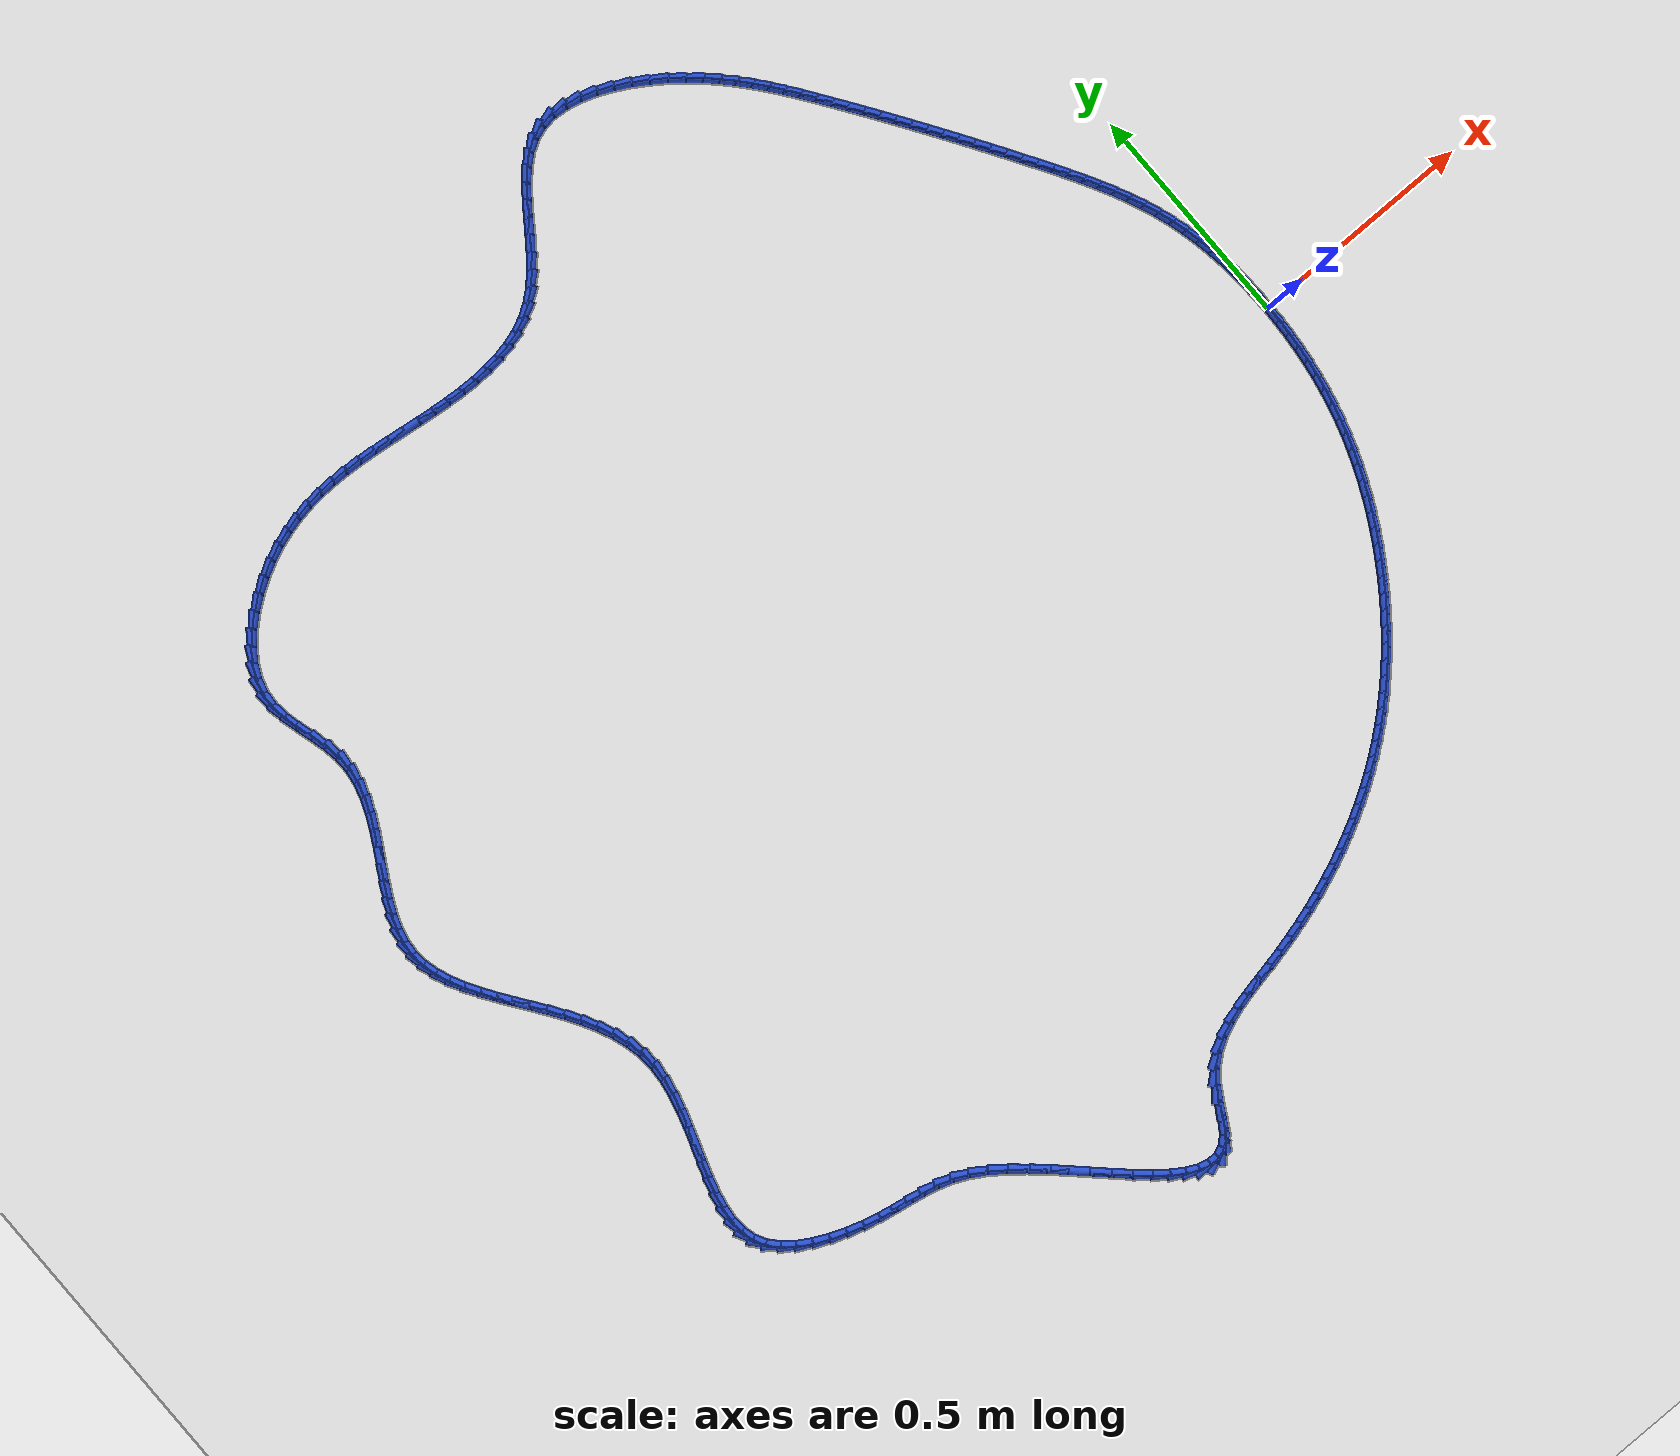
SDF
<sdf version="1.6">
 <world name="default">
  <light name="sun" type="directional">
   <pose>0 0 10 0 -0 0</pose>
   <diffuse>0.8 0.8 0.8 1</diffuse>
   <specular>0.2 0.2 0.2 1</specular>
   <attenuation>
    <range>1000</range>
    <constant>0.9</constant>
    <linear>0.01</linear>
    <quadratic>0.001</quadratic>
   </attenuation>
   <direction>-0.5 0.1 -0.9</direction>
  </light>
  <model name="ground_plane">
   <static>1</static>
   <link name="link">
    <collision name="collision">
     <geometry><plane><normal>0 0 1</normal><size>100 100</size></plane></geometry>
     <surface><friction><ode><mu>100</mu><mu2>50</mu2></ode></friction></surface>
    </collision>
    <visual name="visual">
     <cast_shadows>0</cast_shadows>
     <geometry><plane><normal>0 0 1</normal><size>100 100</size></plane></geometry>
     <material>
      <script><uri>file://media/materials/scripts/gazebo.material</uri><name>Gazebo/WhiteGlow</name></script>
     </material>
    </visual>
   </link>
  </model>
  <gravity>0 0 -9.8</gravity>
  <magnetic_field>6e-06 2.3e-05 -4.2e-05</magnetic_field>
  <atmosphere type="adiabatic"/>
  <physics name="default_physics" default="0" type="ode">
   <max_step_size>0.001</max_step_size>
   <real_time_factor>1</real_time_factor>
   <real_time_update_rate>1000</real_time_update_rate>
  </physics>
  <scene><ambient>0.4 0.4 0.4 1</ambient><background>0.7 0.7 0.7 1</background><shadows>1</shadows></scene>
  <spherical_coordinates>
   <surface_model>EARTH_WGS84</surface_model>
   <latitude_deg>0</latitude_deg>
   <longitude_deg>0</longitude_deg>
   <elevation>0</elevation>
   <heading_deg>0</heading_deg>
  </spherical_coordinates>
  <model name="line">
   <link name="link_0">
    <pose>2.2985086056692694e-17 -1.3877787807814457e-17 0.01 0 1.57 -1.5632398384536728</pose>
    <collision name="collision">
     <geometry><cylinder><radius>0.01</radius><length>0.08</length></cylinder></geometry>
    </collision>
    <visual name="visual">
     <material>
      <script><name>Gazebo/Blue</name><uri>file://media/materials/scripts/gazebo.material</uri></script>
     </material>
     <geometry><cylinder><radius>0.01</radius><length>0.08</length></cylinder></geometry>
    </visual>
   </link>
   <link name="link_1">
    <pose>-0.00025837576314255824 0.034191920063962114 0.01 0 1.57 -1.5312324214005397</pose>
    <collision name="collision">
     <geometry><cylinder><radius>0.01</radius><length>0.08</length></cylinder></geometry>
    </collision>
    <visual name="visual">
     <material>
      <script><name>Gazebo/Blue</name><uri>file://media/materials/scripts/gazebo.material</uri></script>
     </material>
     <geometry><cylinder><radius>0.01</radius><length>0.08</length></cylinder></geometry>
    </visual>
   </link>
   <link name="link_2">
    <pose>-0.0016111040865151283 0.06836504899313049 0.01 0 1.57 -1.49722967650896</pose>
    <collision name="collision">
     <geometry><cylinder><radius>0.01</radius><length>0.08</length></cylinder></geometry>
    </collision>
    <visual name="visual">
     <material>
      <script><name>Gazebo/Blue</name><uri>file://media/materials/scripts/gazebo.material</uri></script>
     </material>
     <geometry><cylinder><radius>0.01</radius><length>0.08</length></cylinder></geometry>
    </visual>
   </link>
   <link name="link_3">
    <pose>-0.004122661577274795 0.10244332973766156 0.01 0 1.57 -1.4610895907378112</pose>
    <collision name="collision">
     <geometry><cylinder><radius>0.01</radius><length>0.08</length></cylinder></geometry>
    </collision>
    <visual name="visual">
     <material>
      <script><name>Gazebo/Blue</name><uri>file://media/materials/scripts/gazebo.material</uri></script>
     </material>
     <geometry><cylinder><radius>0.01</radius><length>0.08</length></cylinder></geometry>
    </visual>
   </link>
   <link name="link_4">
    <pose>-0.007857524842578654 0.13635070524771162 0.01 0 1.57 -1.4226739876428596</pose>
    <collision name="collision">
     <geometry><cylinder><radius>0.01</radius><length>0.08</length></cylinder></geometry>
    </collision>
    <visual name="visual">
     <material>
      <script><name>Gazebo/Blue</name><uri>file://media/materials/scripts/gazebo.material</uri></script>
     </material>
     <geometry><cylinder><radius>0.01</radius><length>0.08</length></cylinder></geometry>
    </visual>
   </link>
   <link name="link_5">
    <pose>-0.012880170489583807 0.17001111847343706 0.01 0 1.57 -1.3818534424990059</pose>
    <collision name="collision">
     <geometry><cylinder><radius>0.01</radius><length>0.08</length></cylinder></geometry>
    </collision>
    <visual name="visual">
     <material>
      <script><name>Gazebo/Blue</name><uri>file://media/materials/scripts/gazebo.material</uri></script>
     </material>
     <geometry><cylinder><radius>0.01</radius><length>0.08</length></cylinder></geometry>
    </visual>
   </link>
   <link name="link_6">
    <pose>-0.019255075125447357 0.20334851236499416 0.01 0 1.57 -1.3385136579555996</pose>
    <collision name="collision">
     <geometry><cylinder><radius>0.01</radius><length>0.08</length></cylinder></geometry>
    </collision>
    <visual name="visual">
     <material>
      <script><name>Gazebo/Blue</name><uri>file://media/materials/scripts/gazebo.material</uri></script>
     </material>
     <geometry><cylinder><radius>0.01</radius><length>0.08</length></cylinder></geometry>
    </visual>
   </link>
   <link name="link_7">
    <pose>-0.027046715357326397 0.23628682987253935 0.01 0 1.57 -1.292563396443888</pose>
    <collision name="collision">
     <geometry><cylinder><radius>0.01</radius><length>0.08</length></cylinder></geometry>
    </collision>
    <visual name="visual">
     <material>
      <script><name>Gazebo/Blue</name><uri>file://media/materials/scripts/gazebo.material</uri></script>
     </material>
     <geometry><cylinder><radius>0.01</radius><length>0.08</length></cylinder></geometry>
    </visual>
   </link>
   <link name="link_8">
    <pose>-0.036319567792378035 0.2687500139462289 0.01 0 1.57 -1.2442207988208127</pose>
    <collision name="collision">
     <geometry><cylinder><radius>0.01</radius><length>0.08</length></cylinder></geometry>
    </collision>
    <visual name="visual">
     <material>
      <script><name>Gazebo/Blue</name><uri>file://media/materials/scripts/gazebo.material</uri></script>
     </material>
     <geometry><cylinder><radius>0.01</radius><length>0.08</length></cylinder></geometry>
    </visual>
   </link>
   <link name="link_9">
    <pose>-0.04712986783984875 0.3006667583414745 0.01 0 1.57 -1.1977359957470655</pose>
    <collision name="collision">
     <geometry><cylinder><radius>0.01</radius><length>0.08</length></cylinder></geometry>
    </collision>
    <visual name="visual">
     <material>
      <script><name>Gazebo/Blue</name><uri>file://media/materials/scripts/gazebo.material</uri></script>
     </material>
     <geometry><cylinder><radius>0.01</radius><length>0.08</length></cylinder></geometry>
    </visual>
   </link>
   <link name="link_10">
    <pose>-0.059408259138107516 0.33203815673073617 0.01 0 1.57 -1.1565471879791045</pose>
    <collision name="collision">
     <geometry><cylinder><radius>0.01</radius><length>0.08</length></cylinder></geometry>
    </collision>
    <visual name="visual">
     <material>
      <script><name>Gazebo/Blue</name><uri>file://media/materials/scripts/gazebo.material</uri></script>
     </material>
     <geometry><cylinder><radius>0.01</radius><length>0.08</length></cylinder></geometry>
    </visual>
   </link>
   <link name="link_11">
    <pose>-0.07298752550513402 0.36292171605964507 0.01 0 1.57 -1.1208220712793802</pose>
    <collision name="collision">
     <geometry><cylinder><radius>0.01</radius><length>0.08</length></cylinder></geometry>
    </collision>
    <visual name="visual">
     <material>
      <script><name>Gazebo/Blue</name><uri>file://media/materials/scripts/gazebo.material</uri></script>
     </material>
     <geometry><cylinder><radius>0.01</radius><length>0.08</length></cylinder></geometry>
    </visual>
   </link>
   <link name="link_12">
    <pose>-0.08769786440917376 0.3933764342274584 0.01 0 1.57 -1.0905584630254996</pose>
    <collision name="collision">
     <geometry><cylinder><radius>0.01</radius><length>0.08</length></cylinder></geometry>
    </collision>
    <visual name="visual">
     <material>
      <script><name>Gazebo/Blue</name><uri>file://media/materials/scripts/gazebo.material</uri></script>
     </material>
     <geometry><cylinder><radius>0.01</radius><length>0.08</length></cylinder></geometry>
    </visual>
   </link>
   <link name="link_13">
    <pose>-0.1033694733184723 0.4234613091334334 0.01 0 1.57 -1.065703235288038</pose>
    <collision name="collision">
     <geometry><cylinder><radius>0.01</radius><length>0.08</length></cylinder></geometry>
    </collision>
    <visual name="visual">
     <material>
      <script><name>Gazebo/Blue</name><uri>file://media/materials/scripts/gazebo.material</uri></script>
     </material>
     <geometry><cylinder><radius>0.01</radius><length>0.08</length></cylinder></geometry>
    </visual>
   </link>
   <link name="link_14">
    <pose>-0.11983254970127509 0.4532353386768273 0.01 0 1.57 -1.046179385439959</pose>
    <collision name="collision">
     <geometry><cylinder><radius>0.01</radius><length>0.08</length></cylinder></geometry>
    </collision>
    <visual name="visual">
     <material>
      <script><name>Gazebo/Blue</name><uri>file://media/materials/scripts/gazebo.material</uri></script>
     </material>
     <geometry><cylinder><radius>0.01</radius><length>0.08</length></cylinder></geometry>
    </visual>
   </link>
   <link name="link_15">
    <pose>-0.13691729102582775 0.48275752075689776 0.01 0 1.57 -1.0319074098540488</pose>
    <collision name="collision">
     <geometry><cylinder><radius>0.01</radius><length>0.08</length></cylinder></geometry>
    </collision>
    <visual name="visual">
     <material>
      <script><name>Gazebo/Blue</name><uri>file://media/materials/scripts/gazebo.material</uri></script>
     </material>
     <geometry><cylinder><radius>0.01</radius><length>0.08</length></cylinder></geometry>
    </visual>
   </link>
   <link name="link_16">
    <pose>-0.15445389476037574 0.5120868532729017 0.01 0 1.57 -1.0228211870344515</pose>
    <collision name="collision">
     <geometry><cylinder><radius>0.01</radius><length>0.08</length></cylinder></geometry>
    </collision>
    <visual name="visual">
     <material>
      <script><name>Gazebo/Blue</name><uri>file://media/materials/scripts/gazebo.material</uri></script>
     </material>
     <geometry><cylinder><radius>0.01</radius><length>0.08</length></cylinder></geometry>
    </visual>
   </link>
   <link name="link_17">
    <pose>-0.17227255837316457 0.5412823341240962 0.01 0 1.57 -1.0181166725889825</pose>
    <collision name="collision">
     <geometry><cylinder><radius>0.01</radius><length>0.08</length></cylinder></geometry>
    </collision>
    <visual name="visual">
     <material>
      <script><name>Gazebo/Blue</name><uri>file://media/materials/scripts/gazebo.material</uri></script>
     </material>
     <geometry><cylinder><radius>0.01</radius><length>0.08</length></cylinder></geometry>
    </visual>
   </link>
   <link name="link_18">
    <pose>-0.1902278542120203 0.5703928199339524 0.01 0 1.57 -1.0143237346631302</pose>
    <collision name="collision">
     <geometry><cylinder><radius>0.01</radius><length>0.08</length></cylinder></geometry>
    </collision>
    <visual name="visual">
     <material>
      <script><name>Gazebo/Blue</name><uri>file://media/materials/scripts/gazebo.material</uri></script>
     </material>
     <geometry><cylinder><radius>0.01</radius><length>0.08</length></cylinder></geometry>
    </visual>
   </link>
   <link name="link_19">
    <pose>-0.2082848515343815 0.5994211946010174 0.01 0 1.57 -1.0104597021589745</pose>
    <collision name="collision">
     <geometry><cylinder><radius>0.01</radius><length>0.08</length></cylinder></geometry>
    </collision>
    <visual name="visual">
     <material>
      <script><name>Gazebo/Blue</name><uri>file://media/materials/scripts/gazebo.material</uri></script>
     </material>
     <geometry><cylinder><radius>0.01</radius><length>0.08</length></cylinder></geometry>
    </visual>
   </link>
   <link name="link_20">
    <pose>-0.22643991498239224 0.6283573214414756 0.01 0 1.57 -1.0065208890052546</pose>
    <collision name="collision">
     <geometry><cylinder><radius>0.01</radius><length>0.08</length></cylinder></geometry>
    </collision>
    <visual name="visual">
     <material>
      <script><name>Gazebo/Blue</name><uri>file://media/materials/scripts/gazebo.material</uri></script>
     </material>
     <geometry><cylinder><radius>0.01</radius><length>0.08</length></cylinder></geometry>
    </visual>
   </link>
   <link name="link_21">
    <pose>-0.24468941120227933 0.6571910629377049 0.01 0 1.57 -1.0025035332740249</pose>
    <collision name="collision">
     <geometry><cylinder><radius>0.01</radius><length>0.08</length></cylinder></geometry>
    </collision>
    <visual name="visual">
     <material>
      <script><name>Gazebo/Blue</name><uri>file://media/materials/scripts/gazebo.material</uri></script>
     </material>
     <geometry><cylinder><radius>0.01</radius><length>0.08</length></cylinder></geometry>
    </visual>
   </link>
   <link name="link_22">
    <pose>-0.26302970684026933 0.685912281572083 0.01 0 1.57 -0.9984037235790574</pose>
    <collision name="collision">
     <geometry><cylinder><radius>0.01</radius><length>0.08</length></cylinder></geometry>
    </collision>
    <visual name="visual">
     <material>
      <script><name>Gazebo/Blue</name><uri>file://media/materials/scripts/gazebo.material</uri></script>
     </material>
     <geometry><cylinder><radius>0.01</radius><length>0.08</length></cylinder></geometry>
    </visual>
   </link>
   <link name="link_23">
    <pose>-0.28145716854258873 0.7145108398269874 0.01 0 1.57 -0.9942173875216094</pose>
    <collision name="collision">
     <geometry><cylinder><radius>0.01</radius><length>0.08</length></cylinder></geometry>
    </collision>
    <visual name="visual">
     <material>
      <script><name>Gazebo/Blue</name><uri>file://media/materials/scripts/gazebo.material</uri></script>
     </material>
     <geometry><cylinder><radius>0.01</radius><length>0.08</length></cylinder></geometry>
    </visual>
   </link>
   <link name="link_24">
    <pose>-0.29996816295546413 0.7429766001847952 0.01 0 1.57 -0.9899402794514747</pose>
    <collision name="collision">
     <geometry><cylinder><radius>0.01</radius><length>0.08</length></cylinder></geometry>
    </collision>
    <visual name="visual">
     <material>
      <script><name>Gazebo/Blue</name><uri>file://media/materials/scripts/gazebo.material</uri></script>
     </material>
     <geometry><cylinder><radius>0.01</radius><length>0.08</length></cylinder></geometry>
    </visual>
   </link>
   <link name="link_25">
    <pose>-0.31855905672512225 0.7712994251278844 0.01 0 1.57 -0.9855679674756073</pose>
    <collision name="collision">
     <geometry><cylinder><radius>0.01</radius><length>0.08</length></cylinder></geometry>
    </collision>
    <visual name="visual">
     <material>
      <script><name>Gazebo/Blue</name><uri>file://media/materials/scripts/gazebo.material</uri></script>
     </material>
     <geometry><cylinder><radius>0.01</radius><length>0.08</length></cylinder></geometry>
    </visual>
   </link>
   <link name="link_26">
    <pose>-0.3372262164977896 0.7994691771386324 0.01 0 1.57 -0.9810958196419883</pose>
    <collision name="collision">
     <geometry><cylinder><radius>0.01</radius><length>0.08</length></cylinder></geometry>
    </collision>
    <visual name="visual">
     <material>
      <script><name>Gazebo/Blue</name><uri>file://media/materials/scripts/gazebo.material</uri></script>
     </material>
     <geometry><cylinder><radius>0.01</radius><length>0.08</length></cylinder></geometry>
    </visual>
   </link>
   <link name="link_27">
    <pose>-0.3559660089196929 0.8274757186994169 0.01 0 1.57 -0.9765189892205798</pose>
    <collision name="collision">
     <geometry><cylinder><radius>0.01</radius><length>0.08</length></cylinder></geometry>
    </collision>
    <visual name="visual">
     <material>
      <script><name>Gazebo/Blue</name><uri>file://media/materials/scripts/gazebo.material</uri></script>
     </material>
     <geometry><cylinder><radius>0.01</radius><length>0.08</length></cylinder></geometry>
    </visual>
   </link>
   <link name="link_28">
    <pose>-0.37477480063705837 0.8553089122926152 0.01 0 1.57 -0.9718323989973517</pose>
    <collision name="collision">
     <geometry><cylinder><radius>0.01</radius><length>0.08</length></cylinder></geometry>
    </collision>
    <visual name="visual">
     <material>
      <script><name>Gazebo/Blue</name><uri>file://media/materials/scripts/gazebo.material</uri></script>
     </material>
     <geometry><cylinder><radius>0.01</radius><length>0.08</length></cylinder></geometry>
    </visual>
   </link>
   <link name="link_29">
    <pose>-0.3936489582961129 0.8829586204006049 0.01 0 1.57 -0.9670307244905849</pose>
    <collision name="collision">
     <geometry><cylinder><radius>0.01</radius><length>0.08</length></cylinder></geometry>
    </collision>
    <visual name="visual">
     <material>
      <script><name>Gazebo/Blue</name><uri>file://media/materials/scripts/gazebo.material</uri></script>
     </material>
     <geometry><cylinder><radius>0.01</radius><length>0.08</length></cylinder></geometry>
    </visual>
   </link>
   <link name="link_30">
    <pose>-0.4125848485430831 0.9104147055057635 0.01 0 1.57 -0.9617721216435963</pose>
    <collision name="collision">
     <geometry><cylinder><radius>0.01</radius><length>0.08</length></cylinder></geometry>
    </collision>
    <visual name="visual">
     <material>
      <script><name>Gazebo/Blue</name><uri>file://media/materials/scripts/gazebo.material</uri></script>
     </material>
     <geometry><cylinder><radius>0.01</radius><length>0.08</length></cylinder></geometry>
    </visual>
   </link>
   <link name="link_31">
    <pose>-0.4315902551562774 0.9376638741381212 0.01 0 1.57 -0.9523835846050901</pose>
    <collision name="collision">
     <geometry><cylinder><radius>0.01</radius><length>0.08</length></cylinder></geometry>
    </collision>
    <visual name="visual">
     <material>
      <script><name>Gazebo/Blue</name><uri>file://media/materials/scripts/gazebo.material</uri></script>
     </material>
     <geometry><cylinder><radius>0.01</radius><length>0.08</length></cylinder></geometry>
    </visual>
   </link>
   <link name="link_32">
    <pose>-0.4507973193872655 0.9646584576223689 0.01 0 1.57 -0.9366248579137219</pose>
    <collision name="collision">
     <geometry><cylinder><radius>0.01</radius><length>0.08</length></cylinder></geometry>
    </collision>
    <visual name="visual">
     <material>
      <script><name>Gazebo/Blue</name><uri>file://media/materials/scripts/gazebo.material</uri></script>
     </material>
     <geometry><cylinder><radius>0.01</radius><length>0.08</length></cylinder></geometry>
    </visual>
   </link>
   <link name="link_33">
    <pose>-0.47041461107264115 0.9913296607016172 0.01 0 1.57 -0.9145557799903085</pose>
    <collision name="collision">
     <geometry><cylinder><radius>0.01</radius><length>0.08</length></cylinder></geometry>
    </collision>
    <visual name="visual">
     <material>
      <script><name>Gazebo/Blue</name><uri>file://media/materials/scripts/gazebo.material</uri></script>
     </material>
     <geometry><cylinder><radius>0.01</radius><length>0.08</length></cylinder></geometry>
    </visual>
   </link>
   <link name="link_34">
    <pose>-0.49065181344204173 1.0176083803520735 0.01 0 1.57 -0.8863747822637508</pose>
    <collision name="collision">
     <geometry><cylinder><radius>0.01</radius><length>0.08</length></cylinder></geometry>
    </collision>
    <visual name="visual">
     <material>
      <script><name>Gazebo/Blue</name><uri>file://media/materials/scripts/gazebo.material</uri></script>
     </material>
     <geometry><cylinder><radius>0.01</radius><length>0.08</length></cylinder></geometry>
    </visual>
   </link>
   <link name="link_35">
    <pose>-0.5117186097251047 1.043425513549945 0.01 0 1.57 -0.8524047128776496</pose>
    <collision name="collision">
     <geometry><cylinder><radius>0.01</radius><length>0.08</length></cylinder></geometry>
    </collision>
    <visual name="visual">
     <material>
      <script><name>Gazebo/Blue</name><uri>file://media/materials/scripts/gazebo.material</uri></script>
     </material>
     <geometry><cylinder><radius>0.01</radius><length>0.08</length></cylinder></geometry>
    </visual>
   </link>
   <link name="link_36">
    <pose>-0.5338246831514674 1.0687119572714385 0.01 0 1.57 -0.8131090265345018</pose>
    <collision name="collision">
     <geometry><cylinder><radius>0.01</radius><length>0.08</length></cylinder></geometry>
    </collision>
    <visual name="visual">
     <material>
      <script><name>Gazebo/Blue</name><uri>file://media/materials/scripts/gazebo.material</uri></script>
     </material>
     <geometry><cylinder><radius>0.01</radius><length>0.08</length></cylinder></geometry>
    </visual>
   </link>
   <link name="link_37">
    <pose>-0.5571797169507671 1.0933986084927616 0.01 0 1.57 -0.7691002343548958</pose>
    <collision name="collision">
     <geometry><cylinder><radius>0.01</radius><length>0.08</length></cylinder></geometry>
    </collision>
    <visual name="visual">
     <material>
      <script><name>Gazebo/Blue</name><uri>file://media/materials/scripts/gazebo.material</uri></script>
     </material>
     <geometry><cylinder><radius>0.01</radius><length>0.08</length></cylinder></geometry>
    </visual>
   </link>
   <link name="link_38">
    <pose>-0.5819933943526411 1.1174163641901216 0.01 0 1.57 -0.7211352103608009</pose>
    <collision name="collision">
     <geometry><cylinder><radius>0.01</radius><length>0.08</length></cylinder></geometry>
    </collision>
    <visual name="visual">
     <material>
      <script><name>Gazebo/Blue</name><uri>file://media/materials/scripts/gazebo.material</uri></script>
     </material>
     <geometry><cylinder><radius>0.01</radius><length>0.08</length></cylinder></geometry>
    </visual>
   </link>
   <link name="link_39">
    <pose>-0.6084753985867271 1.1406961213397255 0.01 0 1.57 -0.6700934895207922</pose>
    <collision name="collision">
     <geometry><cylinder><radius>0.01</radius><length>0.08</length></cylinder></geometry>
    </collision>
    <visual name="visual">
     <material>
      <script><name>Gazebo/Blue</name><uri>file://media/materials/scripts/gazebo.material</uri></script>
     </material>
     <geometry><cylinder><radius>0.01</radius><length>0.08</length></cylinder></geometry>
    </visual>
   </link>
   <link name="link_40">
    <pose>-0.6368354128826623 1.1631687769177808 0.01 0 1.57 -0.6167879068671015</pose>
    <collision name="collision">
     <geometry><cylinder><radius>0.01</radius><length>0.08</length></cylinder></geometry>
    </collision>
    <visual name="visual">
     <material>
      <script><name>Gazebo/Blue</name><uri>file://media/materials/scripts/gazebo.material</uri></script>
     </material>
     <geometry><cylinder><radius>0.01</radius><length>0.08</length></cylinder></geometry>
    </visual>
   </link>
   <link name="link_41">
    <pose>-0.6672229803817051 1.184715716646145 0.01 0 1.57 -0.5598310138124964</pose>
    <collision name="collision">
     <geometry><cylinder><radius>0.01</radius><length>0.08</length></cylinder></geometry>
    </collision>
    <visual name="visual">
     <material>
      <script><name>Gazebo/Blue</name><uri>file://media/materials/scripts/gazebo.material</uri></script>
     </material>
     <geometry><cylinder><radius>0.01</radius><length>0.08</length></cylinder></geometry>
    </visual>
   </link>
   <link name="link_42">
    <pose>-0.6993100388149439 1.204825130234183 0.01 0 1.57 -0.49578492043419625</pose>
    <collision name="collision">
     <geometry><cylinder><radius>0.01</radius><length>0.08</length></cylinder></geometry>
    </collision>
    <visual name="visual">
     <material>
      <script><name>Gazebo/Blue</name><uri>file://media/materials/scripts/gazebo.material</uri></script>
     </material>
     <geometry><cylinder><radius>0.01</radius><length>0.08</length></cylinder></geometry>
    </visual>
   </link>
   <link name="link_43">
    <pose>-0.732540772633907 1.2227977059948165 0.01 0 1.57 -0.4208241884931734</pose>
    <collision name="collision">
     <geometry><cylinder><radius>0.01</radius><length>0.08</length></cylinder></geometry>
    </collision>
    <visual name="visual">
     <material>
      <script><name>Gazebo/Blue</name><uri>file://media/materials/scripts/gazebo.material</uri></script>
     </material>
     <geometry><cylinder><radius>0.01</radius><length>0.08</length></cylinder></geometry>
    </visual>
   </link>
   <link name="link_44">
    <pose>-0.7663579637400014 1.2379329775699712 0.01 0 1.57 -0.3301125623097931</pose>
    <collision name="collision">
     <geometry><cylinder><radius>0.01</radius><length>0.08</length></cylinder></geometry>
    </collision>
    <visual name="visual">
     <material>
      <script><name>Gazebo/Blue</name><uri>file://media/materials/scripts/gazebo.material</uri></script>
     </material>
     <geometry><cylinder><radius>0.01</radius><length>0.08</length></cylinder></geometry>
    </visual>
   </link>
   <link name="link_45">
    <pose>-0.8002043940346338 1.2495304786015733 0.01 0 1.57 -0.21738622132233412</pose>
    <collision name="collision">
     <geometry><cylinder><radius>0.01</radius><length>0.08</length></cylinder></geometry>
    </collision>
    <visual name="visual">
     <material>
      <script><name>Gazebo/Blue</name><uri>file://media/materials/scripts/gazebo.material</uri></script>
     </material>
     <geometry><cylinder><radius>0.01</radius><length>0.08</length></cylinder></geometry>
    </visual>
   </link>
   <link name="link_46">
    <pose>-0.8335228454192106 1.2568897427315466 0.01 0 1.57 -0.07495445857999648</pose>
    <collision name="collision">
     <geometry><cylinder><radius>0.01</radius><length>0.08</length></cylinder></geometry>
    </collision>
    <visual name="visual">
     <material>
      <script><name>Gazebo/Blue</name><uri>file://media/materials/scripts/gazebo.material</uri></script>
     </material>
     <geometry><cylinder><radius>0.01</radius><length>0.08</length></cylinder></geometry>
    </visual>
   </link>
   <link name="link_47">
    <pose>-0.865756099795139 1.2593103036018176 0.01 0 1.57 0.10482910123340287</pose>
    <collision name="collision">
     <geometry><cylinder><radius>0.01</radius><length>0.08</length></cylinder></geometry>
    </collision>
    <visual name="visual">
     <material>
      <script><name>Gazebo/Blue</name><uri>file://media/materials/scripts/gazebo.material</uri></script>
     </material>
     <geometry><cylinder><radius>0.01</radius><length>0.08</length></cylinder></geometry>
    </visual>
   </link>
   <link name="link_48">
    <pose>-0.8963469390638253 1.256091694854311 0.01 0 1.57 0.32334840114601204</pose>
    <collision name="collision">
     <geometry><cylinder><radius>0.01</radius><length>0.08</length></cylinder></geometry>
    </collision>
    <visual name="visual">
     <material>
      <script><name>Gazebo/Blue</name><uri>file://media/materials/scripts/gazebo.material</uri></script>
     </material>
     <geometry><cylinder><radius>0.01</radius><length>0.08</length></cylinder></geometry>
    </visual>
   </link>
   <link name="link_49">
    <pose>-0.9247586474539718 1.246570656738815 0.01 0 1.57 0.5382058156601293</pose>
    <collision name="collision">
     <geometry><cylinder><radius>0.01</radius><length>0.08</length></cylinder></geometry>
    </collision>
    <visual name="visual">
     <material>
      <script><name>Gazebo/Blue</name><uri>file://media/materials/scripts/gazebo.material</uri></script>
     </material>
     <geometry><cylinder><radius>0.01</radius><length>0.08</length></cylinder></geometry>
    </visual>
   </link>
   <link name="link_50">
    <pose>-0.950929878066286 1.230946605383625 0.01 0 1.57 0.7036885023623992</pose>
    <collision name="collision">
     <geometry><cylinder><radius>0.01</radius><length>0.08</length></cylinder></geometry>
    </collision>
    <visual name="visual">
     <material>
      <script><name>Gazebo/Blue</name><uri>file://media/materials/scripts/gazebo.material</uri></script>
     </material>
     <geometry><cylinder><radius>0.01</radius><length>0.08</length></cylinder></geometry>
    </visual>
   </link>
   <link name="link_51">
    <pose>-0.9752767822204232 1.2102854970288819 0.01 0 1.57 0.8197576921429266</pose>
    <collision name="collision">
     <geometry><cylinder><radius>0.01</radius><length>0.08</length></cylinder></geometry>
    </collision>
    <visual name="visual">
     <material>
      <script><name>Gazebo/Blue</name><uri>file://media/materials/scripts/gazebo.material</uri></script>
     </material>
     <geometry><cylinder><radius>0.01</radius><length>0.08</length></cylinder></geometry>
    </visual>
   </link>
   <link name="link_52">
    <pose>-0.9982364394353885 1.1856912673740971 0.01 0 1.57 0.894484077667821</pose>
    <collision name="collision">
     <geometry><cylinder><radius>0.01</radius><length>0.08</length></cylinder></geometry>
    </collision>
    <visual name="visual">
     <material>
      <script><name>Gazebo/Blue</name><uri>file://media/materials/scripts/gazebo.material</uri></script>
     </material>
     <geometry><cylinder><radius>0.01</radius><length>0.08</length></cylinder></geometry>
    </visual>
   </link>
   <link name="link_53">
    <pose>-1.0202459292301882 1.1582678521187832 0.01 0 1.57 0.9353597477938723</pose>
    <collision name="collision">
     <geometry><cylinder><radius>0.01</radius><length>0.08</length></cylinder></geometry>
    </collision>
    <visual name="visual">
     <material>
      <script><name>Gazebo/Blue</name><uri>file://media/materials/scripts/gazebo.material</uri></script>
     </material>
     <geometry><cylinder><radius>0.01</radius><length>0.08</length></cylinder></geometry>
    </visual>
   </link>
   <link name="link_54">
    <pose>-1.0417423311238279 1.1291191869624517 0.01 0 1.57 0.9470828733167915</pose>
    <collision name="collision">
     <geometry><cylinder><radius>0.01</radius><length>0.08</length></cylinder></geometry>
    </collision>
    <visual name="visual">
     <material>
      <script><name>Gazebo/Blue</name><uri>file://media/materials/scripts/gazebo.material</uri></script>
     </material>
     <geometry><cylinder><radius>0.01</radius><length>0.08</length></cylinder></geometry>
    </visual>
   </link>
   <link name="link_55">
    <pose>-1.0631627246353132 1.0993492076046145 0.01 0 1.57 0.9313293873262152</pose>
    <collision name="collision">
     <geometry><cylinder><radius>0.01</radius><length>0.08</length></cylinder></geometry>
    </collision>
    <visual name="visual">
     <material>
      <script><name>Gazebo/Blue</name><uri>file://media/materials/scripts/gazebo.material</uri></script>
     </material>
     <geometry><cylinder><radius>0.01</radius><length>0.08</length></cylinder></geometry>
    </visual>
   </link>
   <link name="link_56">
    <pose>-1.0849441892836496 1.0700618497447834 0.01 0 1.57 0.8869006219384965</pose>
    <collision name="collision">
     <geometry><cylinder><radius>0.01</radius><length>0.08</length></cylinder></geometry>
    </collision>
    <visual name="visual">
     <material>
      <script><name>Gazebo/Blue</name><uri>file://media/materials/scripts/gazebo.material</uri></script>
     </material>
     <geometry><cylinder><radius>0.01</radius><length>0.08</length></cylinder></geometry>
    </visual>
   </link>
   <link name="link_57">
    <pose>-1.1075238045878433 1.0423610490824702 0.01 0 1.57 0.809877830168493</pose>
    <collision name="collision">
     <geometry><cylinder><radius>0.01</radius><length>0.08</length></cylinder></geometry>
    </collision>
    <visual name="visual">
     <material>
      <script><name>Gazebo/Blue</name><uri>file://media/materials/scripts/gazebo.material</uri></script>
     </material>
     <geometry><cylinder><radius>0.01</radius><length>0.08</length></cylinder></geometry>
    </visual>
   </link>
   <link name="link_58">
    <pose>-1.1313386500668998 1.017350741317187 0.01 0 1.57 0.6945707113592207</pose>
    <collision name="collision">
     <geometry><cylinder><radius>0.01</radius><length>0.08</length></cylinder></geometry>
    </collision>
    <visual name="visual">
     <material>
      <script><name>Gazebo/Blue</name><uri>file://media/materials/scripts/gazebo.material</uri></script>
     </material>
     <geometry><cylinder><radius>0.01</radius><length>0.08</length></cylinder></geometry>
    </visual>
   </link>
   <link name="link_59">
    <pose>-1.1568208809657459 0.9961227830435774 0.01 0 1.57 0.5546889701685163</pose>
    <collision name="collision">
     <geometry><cylinder><radius>0.01</radius><length>0.08</length></cylinder></geometry>
    </collision>
    <visual name="visual">
     <material>
      <script><name>Gazebo/Blue</name><uri>file://media/materials/scripts/gazebo.material</uri></script>
     </material>
     <geometry><cylinder><radius>0.01</radius><length>0.08</length></cylinder></geometry>
    </visual>
   </link>
   <link name="link_60">
    <pose>-1.1841633607919964 0.9791820550010722 0.01 0 1.57 0.4203542126535305</pose>
    <collision name="collision">
     <geometry><cylinder><radius>0.01</radius><length>0.08</length></cylinder></geometry>
    </collision>
    <visual name="visual">
     <material>
      <script><name>Gazebo/Blue</name><uri>file://media/materials/scripts/gazebo.material</uri></script>
     </material>
     <geometry><cylinder><radius>0.01</radius><length>0.08</length></cylinder></geometry>
    </visual>
   </link>
   <link name="link_61">
    <pose>-1.2132171776333305 0.9661950725026004 0.01 0 1.57 0.29905972575282286</pose>
    <collision name="collision">
     <geometry><cylinder><radius>0.01</radius><length>0.08</length></cylinder></geometry>
    </collision>
    <visual name="visual">
     <material>
      <script><name>Gazebo/Blue</name><uri>file://media/materials/scripts/gazebo.material</uri></script>
     </material>
     <geometry><cylinder><radius>0.01</radius><length>0.08</length></cylinder></geometry>
    </visual>
   </link>
   <link name="link_62">
    <pose>-1.2438071785914095 0.9567639824655036 0.01 0 1.57 0.1938673856405325</pose>
    <collision name="collision">
     <geometry><cylinder><radius>0.01</radius><length>0.08</length></cylinder></geometry>
    </collision>
    <visual name="visual">
     <material>
      <script><name>Gazebo/Blue</name><uri>file://media/materials/scripts/gazebo.material</uri></script>
     </material>
     <geometry><cylinder><radius>0.01</radius><length>0.08</length></cylinder></geometry>
    </visual>
   </link>
   <link name="link_63">
    <pose>-1.2757582107678975 0.9504909318071219 0.01 0 1.57 0.1056161498923905</pose>
    <collision name="collision">
     <geometry><cylinder><radius>0.01</radius><length>0.08</length></cylinder></geometry>
    </collision>
    <visual name="visual">
     <material>
      <script><name>Gazebo/Blue</name><uri>file://media/materials/scripts/gazebo.material</uri></script>
     </material>
     <geometry><cylinder><radius>0.01</radius><length>0.08</length></cylinder></geometry>
    </visual>
   </link>
   <link name="link_64">
    <pose>-1.3088951212644555 0.9469780674447966 0.01 0 1.57 0.03368010845284562</pose>
    <collision name="collision">
     <geometry><cylinder><radius>0.01</radius><length>0.08</length></cylinder></geometry>
    </collision>
    <visual name="visual">
     <material>
      <script><name>Gazebo/Blue</name><uri>file://media/materials/scripts/gazebo.material</uri></script>
     </material>
     <geometry><cylinder><radius>0.01</radius><length>0.08</length></cylinder></geometry>
    </visual>
   </link>
   <link name="link_65">
    <pose>-1.3430427571827463 0.945827536295868 0.01 0 1.57 -0.02326265055965935</pose>
    <collision name="collision">
     <geometry><cylinder><radius>0.01</radius><length>0.08</length></cylinder></geometry>
    </collision>
    <visual name="visual">
     <material>
      <script><name>Gazebo/Blue</name><uri>file://media/materials/scripts/gazebo.material</uri></script>
     </material>
     <geometry><cylinder><radius>0.01</radius><length>0.08</length></cylinder></geometry>
    </visual>
   </link>
   <link name="link_66">
    <pose>-1.3780259656244327 0.9466414852776776 0.01 0 1.57 -0.06668922177319665</pose>
    <collision name="collision">
     <geometry><cylinder><radius>0.01</radius><length>0.08</length></cylinder></geometry>
    </collision>
    <visual name="visual">
     <material>
      <script><name>Gazebo/Blue</name><uri>file://media/materials/scripts/gazebo.material</uri></script>
     </material>
     <geometry><cylinder><radius>0.01</radius><length>0.08</length></cylinder></geometry>
    </visual>
   </link>
   <link name="link_67">
    <pose>-1.4136695936911763 0.9490220613075656 0.01 0 1.57 -0.0979270749166852</pose>
    <collision name="collision">
     <geometry><cylinder><radius>0.01</radius><length>0.08</length></cylinder></geometry>
    </collision>
    <visual name="visual">
     <material>
      <script><name>Gazebo/Blue</name><uri>file://media/materials/scripts/gazebo.material</uri></script>
     </material>
     <geometry><cylinder><radius>0.01</radius><length>0.08</length></cylinder></geometry>
    </visual>
   </link>
   <link name="link_68">
    <pose>-1.4497984884846407 0.9525714113028732 0.01 0 1.57 -0.1180108050710672</pose>
    <collision name="collision">
     <geometry><cylinder><radius>0.01</radius><length>0.08</length></cylinder></geometry>
    </collision>
    <visual name="visual">
     <material>
      <script><name>Gazebo/Blue</name><uri>file://media/materials/scripts/gazebo.material</uri></script>
     </material>
     <geometry><cylinder><radius>0.01</radius><length>0.08</length></cylinder></geometry>
    </visual>
   </link>
   <link name="link_69">
    <pose>-1.4862374971064871 0.9568916821809412 0.01 0 1.57 -0.1276270603784995</pose>
    <collision name="collision">
     <geometry><cylinder><radius>0.01</radius><length>0.08</length></cylinder></geometry>
    </collision>
    <visual name="visual">
     <material>
      <script><name>Gazebo/Blue</name><uri>file://media/materials/scripts/gazebo.material</uri></script>
     </material>
     <geometry><cylinder><radius>0.01</radius><length>0.08</length></cylinder></geometry>
    </visual>
   </link>
   <link name="link_70">
    <pose>-1.522811466658379 0.9615850208591104 0.01 0 1.57 -0.12709848111222424</pose>
    <collision name="collision">
     <geometry><cylinder><radius>0.01</radius><length>0.08</length></cylinder></geometry>
    </collision>
    <visual name="visual">
     <material>
      <script><name>Gazebo/Blue</name><uri>file://media/materials/scripts/gazebo.material</uri></script>
     </material>
     <geometry><cylinder><radius>0.01</radius><length>0.08</length></cylinder></geometry>
    </visual>
   </link>
   <link name="link_71">
    <pose>-1.5593452442419777 0.9662535742547216 0.01 0 1.57 -0.1163797046956164</pose>
    <collision name="collision">
     <geometry><cylinder><radius>0.01</radius><length>0.08</length></cylinder></geometry>
    </collision>
    <visual name="visual">
     <material>
      <script><name>Gazebo/Blue</name><uri>file://media/materials/scripts/gazebo.material</uri></script>
     </material>
     <geometry><cylinder><radius>0.01</radius><length>0.08</length></cylinder></geometry>
    </visual>
   </link>
   <link name="link_72">
    <pose>-1.595663676958947 0.9704994892851156 0.01 0 1.57 -0.09505419089202705</pose>
    <collision name="collision">
     <geometry><cylinder><radius>0.01</radius><length>0.08</length></cylinder></geometry>
    </collision>
    <visual name="visual">
     <material>
      <script><name>Gazebo/Blue</name><uri>file://media/materials/scripts/gazebo.material</uri></script>
     </material>
     <geometry><cylinder><radius>0.01</radius><length>0.08</length></cylinder></geometry>
    </visual>
   </link>
   <link name="link_73">
    <pose>-1.6315916119109481 0.9739249128676335 0.01 0 1.57 -0.062332516761438174</pose>
    <collision name="collision">
     <geometry><cylinder><radius>0.01</radius><length>0.08</length></cylinder></geometry>
    </collision>
    <visual name="visual">
     <material>
      <script><name>Gazebo/Blue</name><uri>file://media/materials/scripts/gazebo.material</uri></script>
     </material>
     <geometry><cylinder><radius>0.01</radius><length>0.08</length></cylinder></geometry>
    </visual>
   </link>
   <link name="link_74">
    <pose>-1.6669538966825557 0.9761319922364173 0.01 0 1.57 -0.017990658891426033</pose>
    <collision name="collision">
     <geometry><cylinder><radius>0.01</radius><length>0.08</length></cylinder></geometry>
    </collision>
    <visual name="visual">
     <material>
      <script><name>Gazebo/Blue</name><uri>file://media/materials/scripts/gazebo.material</uri></script>
     </material>
     <geometry><cylinder><radius>0.01</radius><length>0.08</length></cylinder></geometry>
    </visual>
   </link>
   <link name="link_75">
    <pose>-1.7016256084986192 0.9767558264825233 0.01 0 1.57 0.03525739152219126</pose>
    <collision name="collision">
     <geometry><cylinder><radius>0.01</radius><length>0.08</length></cylinder></geometry>
    </collision>
    <visual name="visual">
     <material>
      <script><name>Gazebo/Blue</name><uri>file://media/materials/scripts/gazebo.material</uri></script>
     </material>
     <geometry><cylinder><radius>0.01</radius><length>0.08</length></cylinder></geometry>
    </visual>
   </link>
   <link name="link_76">
    <pose>-1.7356700724963374 0.9755550098731188 0.01 0 1.57 0.09628548511236039</pose>
    <collision name="collision">
     <geometry><cylinder><radius>0.01</radius><length>0.08</length></cylinder></geometry>
    </collision>
    <visual name="visual">
     <material>
      <script><name>Gazebo/Blue</name><uri>file://media/materials/scripts/gazebo.material</uri></script>
     </material>
     <geometry><cylinder><radius>0.01</radius><length>0.08</length></cylinder></geometry>
    </visual>
   </link>
   <link name="link_77">
    <pose>-1.7691947055260897 0.9723170619038982 0.01 0 1.57 0.16423341947658976</pose>
    <collision name="collision">
     <geometry><cylinder><radius>0.01</radius><length>0.08</length></cylinder></geometry>
    </collision>
    <visual name="visual">
     <material>
      <script><name>Gazebo/Blue</name><uri>file://media/materials/scripts/gazebo.material</uri></script>
     </material>
     <geometry><cylinder><radius>0.01</radius><length>0.08</length></cylinder></geometry>
    </visual>
   </link>
   <link name="link_78">
    <pose>-1.8023069244382541 0.9668295020705554 0.01 0 1.57 0.23773189081102367</pose>
    <collision name="collision">
     <geometry><cylinder><radius>0.01</radius><length>0.08</length></cylinder></geometry>
    </collision>
    <visual name="visual">
     <material>
      <script><name>Gazebo/Blue</name><uri>file://media/materials/scripts/gazebo.material</uri></script>
     </material>
     <geometry><cylinder><radius>0.01</radius><length>0.08</length></cylinder></geometry>
    </visual>
   </link>
   <link name="link_79">
    <pose>-1.8351141460832086 0.9588798498687842 0.01 0 1.57 0.3149554113314245</pose>
    <collision name="collision">
     <geometry><cylinder><radius>0.01</radius><length>0.08</length></cylinder></geometry>
    </collision>
    <visual name="visual">
     <material>
      <script><name>Gazebo/Blue</name><uri>file://media/materials/scripts/gazebo.material</uri></script>
     </material>
     <geometry><cylinder><radius>0.01</radius><length>0.08</length></cylinder></geometry>
    </visual>
   </link>
   <link name="link_80">
    <pose>-1.8677237873113326 0.9482556247942784 0.01 0 1.57 0.3937818215334405</pose>
    <collision name="collision">
     <geometry><cylinder><radius>0.01</radius><length>0.08</length></cylinder></geometry>
    </collision>
    <visual name="visual">
     <material>
      <script><name>Gazebo/Blue</name><uri>file://media/materials/scripts/gazebo.material</uri></script>
     </material>
     <geometry><cylinder><radius>0.01</radius><length>0.08</length></cylinder></geometry>
    </visual>
   </link>
   <link name="link_81">
    <pose>-1.900243264973004 0.9347443463427324 0.01 0 1.57 0.47206296331955294</pose>
    <collision name="collision">
     <geometry><cylinder><radius>0.01</radius><length>0.08</length></cylinder></geometry>
    </collision>
    <visual name="visual">
     <material>
      <script><name>Gazebo/Blue</name><uri>file://media/materials/scripts/gazebo.material</uri></script>
     </material>
     <geometry><cylinder><radius>0.01</radius><length>0.08</length></cylinder></geometry>
    </visual>
   </link>
   <link name="link_82">
    <pose>-1.9326781822910863 0.9181842487292804 0.01 0 1.57 0.5501377935742998</pose>
    <collision name="collision">
     <geometry><cylinder><radius>0.01</radius><length>0.08</length></cylinder></geometry>
    </collision>
    <visual name="visual">
     <material>
      <script><name>Gazebo/Blue</name><uri>file://media/materials/scripts/gazebo.material</uri></script>
     </material>
     <geometry><cylinder><radius>0.01</radius><length>0.08</length></cylinder></geometry>
    </visual>
   </link>
   <link name="link_83">
    <pose>-1.9643998377487555 0.8987295217802873 0.01 0 1.57 0.6321894082180952</pose>
    <collision name="collision">
     <geometry><cylinder><radius>0.01</radius><length>0.08</length></cylinder></geometry>
    </collision>
    <visual name="visual">
     <material>
      <script><name>Gazebo/Blue</name><uri>file://media/materials/scripts/gazebo.material</uri></script>
     </material>
     <geometry><cylinder><radius>0.01</radius><length>0.08</length></cylinder></geometry>
    </visual>
   </link>
   <link name="link_84">
    <pose>-1.9945356732817079 0.876655823505612 0.01 0 1.57 0.7228964734891816</pose>
    <collision name="collision">
     <geometry><cylinder><radius>0.01</radius><length>0.08</length></cylinder></geometry>
    </collision>
    <visual name="visual">
     <material>
      <script><name>Gazebo/Blue</name><uri>file://media/materials/scripts/gazebo.material</uri></script>
     </material>
     <geometry><cylinder><radius>0.01</radius><length>0.08</length></cylinder></geometry>
    </visual>
   </link>
   <link name="link_85">
    <pose>-2.0222126232435707 0.8522390647484794 0.01 0 1.57 0.8274539265994267</pose>
    <collision name="collision">
     <geometry><cylinder><radius>0.01</radius><length>0.08</length></cylinder></geometry>
    </collision>
    <visual name="visual">
     <material>
      <script><name>Gazebo/Blue</name><uri>file://media/materials/scripts/gazebo.material</uri></script>
     </material>
     <geometry><cylinder><radius>0.01</radius><length>0.08</length></cylinder></geometry>
    </visual>
   </link>
   <link name="link_86">
    <pose>-2.0465576219879704 0.8257551563521163 0.01 0 1.57 0.9518724542747022</pose>
    <collision name="collision">
     <geometry><cylinder><radius>0.01</radius><length>0.08</length></cylinder></geometry>
    </collision>
    <visual name="visual">
     <material>
      <script><name>Gazebo/Blue</name><uri>file://media/materials/scripts/gazebo.material</uri></script>
     </material>
     <geometry><cylinder><radius>0.01</radius><length>0.08</length></cylinder></geometry>
    </visual>
   </link>
   <link name="link_87">
    <pose>-2.066697603868534 0.7974800091597478 0.01 0 1.57 1.1026831677587619</pose>
    <collision name="collision">
     <geometry><cylinder><radius>0.01</radius><length>0.08</length></cylinder></geometry>
    </collision>
    <visual name="visual">
     <material>
      <script><name>Gazebo/Blue</name><uri>file://media/materials/scripts/gazebo.material</uri></script>
     </material>
     <geometry><cylinder><radius>0.01</radius><length>0.08</length></cylinder></geometry>
    </visual>
   </link>
   <link name="link_88">
    <pose>-2.0817595032388874 0.7676895340146 0.01 0 1.57 1.285210263440374</pose>
    <collision name="collision">
     <geometry><cylinder><radius>0.01</radius><length>0.08</length></cylinder></geometry>
    </collision>
    <visual name="visual">
     <material>
      <script><name>Gazebo/Blue</name><uri>file://media/materials/scripts/gazebo.material</uri></script>
     </material>
     <geometry><cylinder><radius>0.01</radius><length>0.08</length></cylinder></geometry>
    </visual>
   </link>
   <link name="link_89">
    <pose>-2.090870254452658 0.7366596417598984 0.01 0 1.57 1.4976940230537592</pose>
    <collision name="collision">
     <geometry><cylinder><radius>0.01</radius><length>0.08</length></cylinder></geometry>
    </collision>
    <visual name="visual">
     <material>
      <script><name>Gazebo/Blue</name><uri>file://media/materials/scripts/gazebo.material</uri></script>
     </material>
     <geometry><cylinder><radius>0.01</radius><length>0.08</length></cylinder></geometry>
    </visual>
   </link>
   <link name="link_90">
    <pose>-2.0932133261800767 0.7046648020656374 0.01 0 1.57 -1.4557817368991162</pose>
    <collision name="collision">
     <geometry><cylinder><radius>0.01</radius><length>0.08</length></cylinder></geometry>
    </collision>
    <visual name="visual">
     <material>
      <script><name>Gazebo/Blue</name><uri>file://media/materials/scripts/gazebo.material</uri></script>
     </material>
     <geometry><cylinder><radius>0.01</radius><length>0.08</length></cylinder></geometry>
    </visual>
   </link>
   <link name="link_91">
    <pose>-2.089433070981387 0.6719422437384956 0.01 0 1.57 -1.3431574219906954</pose>
    <collision name="collision">
     <geometry><cylinder><radius>0.01</radius><length>0.08</length></cylinder></geometry>
    </collision>
    <visual name="visual">
     <material>
      <script><name>Gazebo/Blue</name><uri>file://media/materials/scripts/gazebo.material</uri></script>
     </material>
     <geometry><cylinder><radius>0.01</radius><length>0.08</length></cylinder></geometry>
    </visual>
   </link>
   <link name="link_92">
    <pose>-2.0817299397385627 0.6386895275148157 0.01 0 1.57 -1.2992921558150217</pose>
    <collision name="collision">
     <geometry><cylinder><radius>0.01</radius><length>0.08</length></cylinder></geometry>
    </collision>
    <visual name="visual">
     <material>
      <script><name>Gazebo/Blue</name><uri>file://media/materials/scripts/gazebo.material</uri></script>
     </material>
     <geometry><cylinder><radius>0.01</radius><length>0.08</length></cylinder></geometry>
    </visual>
   </link>
   <link name="link_93">
    <pose>-2.0723799843383266 0.6051022869095473 0.01 0 1.57 -1.3177636886813704</pose>
    <collision name="collision">
     <geometry><cylinder><radius>0.01</radius><length>0.08</length></cylinder></geometry>
    </collision>
    <visual name="visual">
     <material>
      <script><name>Gazebo/Blue</name><uri>file://media/materials/scripts/gazebo.material</uri></script>
     </material>
     <geometry><cylinder><radius>0.01</radius><length>0.08</length></cylinder></geometry>
    </visual>
   </link>
   <link name="link_94">
    <pose>-2.0636592566674 0.5713761554376411 0.01 0 1.57 -1.3997617094479857</pose>
    <collision name="collision">
     <geometry><cylinder><radius>0.01</radius><length>0.08</length></cylinder></geometry>
    </collision>
    <visual name="visual">
     <material>
      <script><name>Gazebo/Blue</name><uri>file://media/materials/scripts/gazebo.material</uri></script>
     </material>
     <geometry><cylinder><radius>0.01</radius><length>0.08</length></cylinder></geometry>
    </visual>
   </link>
   <link name="link_95">
    <pose>-2.0578438086125046 0.5377067666140458 0.01 0 1.57 -1.5486019473364347</pose>
    <collision name="collision">
     <geometry><cylinder><radius>0.01</radius><length>0.08</length></cylinder></geometry>
    </collision>
    <visual name="visual">
     <material>
      <script><name>Gazebo/Blue</name><uri>file://media/materials/scripts/gazebo.material</uri></script>
     </material>
     <geometry><cylinder><radius>0.01</radius><length>0.08</length></cylinder></geometry>
    </visual>
   </link>
   <link name="link_96">
    <pose>-2.0571018682112534 0.5042830534447099 0.01 0 1.57 1.4273186416940131</pose>
    <collision name="collision">
     <geometry><cylinder><radius>0.01</radius><length>0.08</length></cylinder></geometry>
    </collision>
    <visual name="visual">
     <material>
      <script><name>Gazebo/Blue</name><uri>file://media/materials/scripts/gazebo.material</uri></script>
     </material>
     <geometry><cylinder><radius>0.01</radius><length>0.08</length></cylinder></geometry>
    </visual>
   </link>
   <link name="link_97">
    <pose>-2.061883244913855 0.4711871610652633 0.01 0 1.57 1.2921449384422197</pose>
    <collision name="collision">
     <geometry><cylinder><radius>0.01</radius><length>0.08</length></cylinder></geometry>
    </collision>
    <visual name="visual">
     <material>
      <script><name>Gazebo/Blue</name><uri>file://media/materials/scripts/gazebo.material</uri></script>
     </material>
     <geometry><cylinder><radius>0.01</radius><length>0.08</length></cylinder></geometry>
    </visual>
   </link>
   <link name="link_98">
    <pose>-2.071259029381335 0.4384155567419615 0.01 0 1.57 1.189728829844619</pose>
    <collision name="collision">
     <geometry><cylinder><radius>0.01</radius><length>0.08</length></cylinder></geometry>
    </collision>
    <visual name="visual">
     <material>
      <script><name>Gazebo/Blue</name><uri>file://media/materials/scripts/gazebo.material</uri></script>
     </material>
     <geometry><cylinder><radius>0.01</radius><length>0.08</length></cylinder></geometry>
    </visual>
   </link>
   <link name="link_99">
    <pose>-2.0842614632039114 0.40596229353909385 0.01 0 1.57 1.1173833883756448</pose>
    <collision name="collision">
     <geometry><cylinder><radius>0.01</radius><length>0.08</length></cylinder></geometry>
    </collision>
    <visual name="visual">
     <material>
      <script><name>Gazebo/Blue</name><uri>file://media/materials/scripts/gazebo.material</uri></script>
     </material>
     <geometry><cylinder><radius>0.01</radius><length>0.08</length></cylinder></geometry>
    </visual>
   </link>
   <link name="link_100">
    <pose>-2.0999227879718028 0.37382142452094735 0.01 0 1.57 1.0717346637980592</pose>
    <collision name="collision">
     <geometry><cylinder><radius>0.01</radius><length>0.08</length></cylinder></geometry>
    </collision>
    <visual name="visual">
     <material>
      <script><name>Gazebo/Blue</name><uri>file://media/materials/scripts/gazebo.material</uri></script>
     </material>
     <geometry><cylinder><radius>0.01</radius><length>0.08</length></cylinder></geometry>
    </visual>
   </link>
   <link name="link_101">
    <pose>-2.117275245275225 0.3419870027518112 0.01 0 1.57 1.0503018201952778</pose>
    <collision name="collision">
     <geometry><cylinder><radius>0.01</radius><length>0.08</length></cylinder></geometry>
    </collision>
    <visual name="visual">
     <material>
      <script><name>Gazebo/Blue</name><uri>file://media/materials/scripts/gazebo.material</uri></script>
     </material>
     <geometry><cylinder><radius>0.01</radius><length>0.08</length></cylinder></geometry>
    </visual>
   </link>
   <link name="link_102">
    <pose>-2.135351076704397 0.3104530812959727 0.01 0 1.57 1.0521238044113388</pose>
    <collision name="collision">
     <geometry><cylinder><radius>0.01</radius><length>0.08</length></cylinder></geometry>
    </collision>
    <visual name="visual">
     <material>
      <script><name>Gazebo/Blue</name><uri>file://media/materials/scripts/gazebo.material</uri></script>
     </material>
     <geometry><cylinder><radius>0.01</radius><length>0.08</length></cylinder></geometry>
    </visual>
   </link>
   <link name="link_103">
    <pose>-2.153182523849535 0.27921371321772087 0.01 0 1.57 1.0780201383303796</pose>
    <collision name="collision">
     <geometry><cylinder><radius>0.01</radius><length>0.08</length></cylinder></geometry>
    </collision>
    <visual name="visual">
     <material>
      <script><name>Gazebo/Blue</name><uri>file://media/materials/scripts/gazebo.material</uri></script>
     </material>
     <geometry><cylinder><radius>0.01</radius><length>0.08</length></cylinder></geometry>
    </visual>
   </link>
   <link name="link_104">
    <pose>-2.1698018283008587 0.24826295158134307 0.01 0 1.57 1.1307574098980127</pose>
    <collision name="collision">
     <geometry><cylinder><radius>0.01</radius><length>0.08</length></cylinder></geometry>
    </collision>
    <visual name="visual">
     <material>
      <script><name>Gazebo/Blue</name><uri>file://media/materials/scripts/gazebo.material</uri></script>
     </material>
     <geometry><cylinder><radius>0.01</radius><length>0.08</length></cylinder></geometry>
    </visual>
   </link>
   <link name="link_105">
    <pose>-2.1842412316485835 0.21759484945112825 0.01 0 1.57 1.2150588557051578</pose>
    <collision name="collision">
     <geometry><cylinder><radius>0.01</radius><length>0.08</length></cylinder></geometry>
    </collision>
    <visual name="visual">
     <material>
      <script><name>Gazebo/Blue</name><uri>file://media/materials/scripts/gazebo.material</uri></script>
     </material>
     <geometry><cylinder><radius>0.01</radius><length>0.08</length></cylinder></geometry>
    </visual>
   </link>
   <link name="link_106">
    <pose>-2.1955329754829283 0.18720345989136383 0.01 0 1.57 1.33690395036792</pose>
    <collision name="collision">
     <geometry><cylinder><radius>0.01</radius><length>0.08</length></cylinder></geometry>
    </collision>
    <visual name="visual">
     <material>
      <script><name>Gazebo/Blue</name><uri>file://media/materials/scripts/gazebo.material</uri></script>
     </material>
     <geometry><cylinder><radius>0.01</radius><length>0.08</length></cylinder></geometry>
    </visual>
   </link>
   <link name="link_107">
    <pose>-2.2027093013941106 0.15708283596633874 0.01 0 1.57 1.4996306879586054</pose>
    <collision name="collision">
     <geometry><cylinder><radius>0.01</radius><length>0.08</length></cylinder></geometry>
    </collision>
    <visual name="visual">
     <material>
      <script><name>Gazebo/Blue</name><uri>file://media/materials/scripts/gazebo.material</uri></script>
     </material>
     <geometry><cylinder><radius>0.01</radius><length>0.08</length></cylinder></geometry>
    </visual>
   </link>
   <link name="link_108">
    <pose>-2.20483770143251 0.12722565023418242 0.01 0 1.57 -1.4676700445481352</pose>
    <collision name="collision">
     <geometry><cylinder><radius>0.01</radius><length>0.08</length></cylinder></geometry>
    </collision>
    <visual name="visual">
     <material>
      <script><name>Gazebo/Blue</name><uri>file://media/materials/scripts/gazebo.material</uri></script>
     </material>
     <geometry><cylinder><radius>0.01</radius><length>0.08</length></cylinder></geometry>
    </visual>
   </link>
   <link name="link_109">
    <pose>-2.201771001683867 0.09759381938581346 0.01 0 1.57 -1.3172524718421506</pose>
    <collision name="collision">
     <geometry><cylinder><radius>0.01</radius><length>0.08</length></cylinder></geometry>
    </collision>
    <visual name="visual">
     <material>
      <script><name>Gazebo/Blue</name><uri>file://media/materials/scripts/gazebo.material</uri></script>
     </material>
     <geometry><cylinder><radius>0.01</radius><length>0.08</length></cylinder></geometry>
    </visual>
   </link>
   <link name="link_110">
    <pose>-2.1941334908738903 0.06811904748739894 0.01 0 1.57 -1.1962695192995012</pose>
    <collision name="collision">
     <geometry><cylinder><radius>0.01</radius><length>0.08</length></cylinder></geometry>
    </collision>
    <visual name="visual">
     <material>
      <script><name>Gazebo/Blue</name><uri>file://media/materials/scripts/gazebo.material</uri></script>
     </material>
     <geometry><cylinder><radius>0.01</radius><length>0.08</length></cylinder></geometry>
    </visual>
   </link>
   <link name="link_111">
    <pose>-2.1825819336331658 0.03873176675825847 0.01 0 1.57 -1.1037724015867634</pose>
    <collision name="collision">
     <geometry><cylinder><radius>0.01</radius><length>0.08</length></cylinder></geometry>
    </collision>
    <visual name="visual">
     <material>
      <script><name>Gazebo/Blue</name><uri>file://media/materials/scripts/gazebo.material</uri></script>
     </material>
     <geometry><cylinder><radius>0.01</radius><length>0.08</length></cylinder></geometry>
    </visual>
   </link>
   <link name="link_112">
    <pose>-2.167773094592282 0.009362409417710695 0.01 0 1.57 -1.0364782175728104</pose>
    <collision name="collision">
     <geometry><cylinder><radius>0.01</radius><length>0.08</length></cylinder></geometry>
    </collision>
    <visual name="visual">
     <material>
      <script><name>Gazebo/Blue</name><uri>file://media/materials/scripts/gazebo.material</uri></script>
     </material>
     <geometry><cylinder><radius>0.01</radius><length>0.08</length></cylinder></geometry>
    </visual>
   </link>
   <link name="link_113">
    <pose>-2.1503637383818255 -0.020058592314925537 0.01 0 1.57 -0.9908441151376155</pose>
    <collision name="collision">
     <geometry><cylinder><radius>0.01</radius><length>0.08</length></cylinder></geometry>
    </collision>
    <visual name="visual">
     <material>
      <script><name>Gazebo/Blue</name><uri>file://media/materials/scripts/gazebo.material</uri></script>
     </material>
     <geometry><cylinder><radius>0.01</radius><length>0.08</length></cylinder></geometry>
    </visual>
   </link>
   <link name="link_114">
    <pose>-2.131010629632385 -0.04960080622033193 0.01 0 1.57 -0.9639860256615724</pose>
    <collision name="collision">
     <geometry><cylinder><radius>0.01</radius><length>0.08</length></cylinder></geometry>
    </collision>
    <visual name="visual">
     <material>
      <script><name>Gazebo/Blue</name><uri>file://media/materials/scripts/gazebo.material</uri></script>
     </material>
     <geometry><cylinder><radius>0.01</radius><length>0.08</length></cylinder></geometry>
    </visual>
   </link>
   <link name="link_115">
    <pose>-2.1103705329745486 -0.07933380007918817 0.01 0 1.57 -0.9539437656592163</pose>
    <collision name="collision">
     <geometry><cylinder><radius>0.01</radius><length>0.08</length></cylinder></geometry>
    </collision>
    <visual name="visual">
     <material>
      <script><name>Gazebo/Blue</name><uri>file://media/materials/scripts/gazebo.material</uri></script>
     </material>
     <geometry><cylinder><radius>0.01</radius><length>0.08</length></cylinder></geometry>
    </visual>
   </link>
   <link name="link_116">
    <pose>-2.0891002130389036 -0.10932714167217603 0.01 0 1.57 -0.9596831728577317</pose>
    <collision name="collision">
     <geometry><cylinder><radius>0.01</radius><length>0.08</length></cylinder></geometry>
    </collision>
    <visual name="visual">
     <material>
      <script><name>Gazebo/Blue</name><uri>file://media/materials/scripts/gazebo.material</uri></script>
     </material>
     <geometry><cylinder><radius>0.01</radius><length>0.08</length></cylinder></geometry>
    </visual>
   </link>
   <link name="link_117">
    <pose>-2.067856434456038 -0.13965039877997656 0.01 0 1.57 -0.9810236113031803</pose>
    <collision name="collision">
     <geometry><cylinder><radius>0.01</radius><length>0.08</length></cylinder></geometry>
    </collision>
    <visual name="visual">
     <material>
      <script><name>Gazebo/Blue</name><uri>file://media/materials/scripts/gazebo.material</uri></script>
     </material>
     <geometry><cylinder><radius>0.01</radius><length>0.08</length></cylinder></geometry>
    </visual>
   </link>
   <link name="link_118">
    <pose>-2.0472959618565394 -0.17037313918327163 0.01 0 1.57 -1.0185496766957975</pose>
    <collision name="collision">
     <geometry><cylinder><radius>0.01</radius><length>0.08</length></cylinder></geometry>
    </collision>
    <visual name="visual">
     <material>
      <script><name>Gazebo/Blue</name><uri>file://media/materials/scripts/gazebo.material</uri></script>
     </material>
     <geometry><cylinder><radius>0.01</radius><length>0.08</length></cylinder></geometry>
    </visual>
   </link>
   <link name="link_119">
    <pose>-2.028075559870996 -0.2015649306627407 0.01 0 1.57 -1.073490444505903</pose>
    <collision name="collision">
     <geometry><cylinder><radius>0.01</radius><length>0.08</length></cylinder></geometry>
    </collision>
    <visual name="visual">
     <material>
      <script><name>Gazebo/Blue</name><uri>file://media/materials/scripts/gazebo.material</uri></script>
     </material>
     <geometry><cylinder><radius>0.01</radius><length>0.08</length></cylinder></geometry>
    </visual>
   </link>
   <link name="link_120">
    <pose>-2.0108519931299957 -0.23329534099906563 0.01 0 1.57 -1.1474899468940776</pose>
    <collision name="collision">
     <geometry><cylinder><radius>0.01</radius><length>0.08</length></cylinder></geometry>
    </collision>
    <visual name="visual">
     <material>
      <script><name>Gazebo/Blue</name><uri>file://media/materials/scripts/gazebo.material</uri></script>
     </material>
     <geometry><cylinder><radius>0.01</radius><length>0.08</length></cylinder></geometry>
    </visual>
   </link>
   <link name="link_121">
    <pose>-1.9962820262641254 -0.26563393797292756 0.01 0 1.57 -1.242133862034232</pose>
    <collision name="collision">
     <geometry><cylinder><radius>0.01</radius><length>0.08</length></cylinder></geometry>
    </collision>
    <visual name="visual">
     <material>
      <script><name>Gazebo/Blue</name><uri>file://media/materials/scripts/gazebo.material</uri></script>
     </material>
     <geometry><cylinder><radius>0.01</radius><length>0.08</length></cylinder></geometry>
    </visual>
   </link>
   <link name="link_122">
    <pose>-1.9850224239039735 -0.29865028936500826 0.01 0 1.57 -1.3580781365805008</pose>
    <collision name="collision">
     <geometry><cylinder><radius>0.01</radius><length>0.08</length></cylinder></geometry>
    </collision>
    <visual name="visual">
     <material>
      <script><name>Gazebo/Blue</name><uri>file://media/materials/scripts/gazebo.material</uri></script>
     </material>
     <geometry><cylinder><radius>0.01</radius><length>0.08</length></cylinder></geometry>
    </visual>
   </link>
   <link name="link_123">
    <pose>-1.977729950680128 -0.33241396295598724 0.01 0 1.57 -1.4936648633138763</pose>
    <collision name="collision">
     <geometry><cylinder><radius>0.01</radius><length>0.08</length></cylinder></geometry>
    </collision>
    <visual name="visual">
     <material>
      <script><name>Gazebo/Blue</name><uri>file://media/materials/scripts/gazebo.material</uri></script>
     </material>
     <geometry><cylinder><radius>0.01</radius><length>0.08</length></cylinder></geometry>
    </visual>
   </link>
   <link name="link_124">
    <pose>-1.9750574603203226 -0.36699373564389653 0.01 0 1.57 1.5114983112696694</pose>
    <collision name="collision">
     <geometry><cylinder><radius>0.01</radius><length>0.08</length></cylinder></geometry>
    </collision>
    <visual name="visual">
     <material>
      <script><name>Gazebo/Blue</name><uri>file://media/materials/scripts/gazebo.material</uri></script>
     </material>
     <geometry><cylinder><radius>0.01</radius><length>0.08</length></cylinder></geometry>
    </visual>
   </link>
   <link name="link_125">
    <pose>-1.9771568982398966 -0.4023570881022692 0.01 0 1.57 1.404308357052385</pose>
    <collision name="collision">
     <geometry><cylinder><radius>0.01</radius><length>0.08</length></cylinder></geometry>
    </collision>
    <visual name="visual">
     <material>
      <script><name>Gazebo/Blue</name><uri>file://media/materials/scripts/gazebo.material</uri></script>
     </material>
     <geometry><cylinder><radius>0.01</radius><length>0.08</length></cylinder></geometry>
    </visual>
   </link>
   <link name="link_126">
    <pose>-1.9831921113290971 -0.4382716826994783 0.01 0 1.57 1.3266853729686083</pose>
    <collision name="collision">
     <geometry><cylinder><radius>0.01</radius><length>0.08</length></cylinder></geometry>
    </collision>
    <visual name="visual">
     <material>
      <script><name>Gazebo/Blue</name><uri>file://media/materials/scripts/gazebo.material</uri></script>
     </material>
     <geometry><cylinder><radius>0.01</radius><length>0.08</length></cylinder></geometry>
    </visual>
   </link>
   <link name="link_127">
    <pose>-1.9922112611326033 -0.47448178732541196 0.01 0 1.57 1.2748840542999573</pose>
    <collision name="collision">
     <geometry><cylinder><radius>0.01</radius><length>0.08</length></cylinder></geometry>
    </collision>
    <visual name="visual">
     <material>
      <script><name>Gazebo/Blue</name><uri>file://media/materials/scripts/gazebo.material</uri></script>
     </material>
     <geometry><cylinder><radius>0.01</radius><length>0.08</length></cylinder></geometry>
    </visual>
   </link>
   <link name="link_128">
    <pose>-2.0032625091950926 -0.5107316698699611 0.01 0 1.57 1.24604665164331</pose>
    <collision name="collision">
     <geometry><cylinder><radius>0.01</radius><length>0.08</length></cylinder></geometry>
    </collision>
    <visual name="visual">
     <material>
      <script><name>Gazebo/Blue</name><uri>file://media/materials/scripts/gazebo.material</uri></script>
     </material>
     <geometry><cylinder><radius>0.01</radius><length>0.08</length></cylinder></geometry>
    </visual>
   </link>
   <link name="link_129">
    <pose>-2.015394017061244 -0.5467655982230155 0.01 0 1.57 1.2388100657503465</pose>
    <collision name="collision">
     <geometry><cylinder><radius>0.01</radius><length>0.08</length></cylinder></geometry>
    </collision>
    <visual name="visual">
     <material>
      <script><name>Gazebo/Blue</name><uri>file://media/materials/scripts/gazebo.material</uri></script>
     </material>
     <geometry><cylinder><radius>0.01</radius><length>0.08</length></cylinder></geometry>
    </visual>
   </link>
   <link name="link_130">
    <pose>-2.0276539462757364 -0.582327840274465 0.01 0 1.57 1.2535763853824529</pose>
    <collision name="collision">
     <geometry><cylinder><radius>0.01</radius><length>0.08</length></cylinder></geometry>
    </collision>
    <visual name="visual">
     <material>
      <script><name>Gazebo/Blue</name><uri>file://media/materials/scripts/gazebo.material</uri></script>
     </material>
     <geometry><cylinder><radius>0.01</radius><length>0.08</length></cylinder></geometry>
    </visual>
   </link>
   <link name="link_131">
    <pose>-2.0390904583832477 -0.6171626639142007 0.01 0 1.57 1.2927875573959584</pose>
    <collision name="collision">
     <geometry><cylinder><radius>0.01</radius><length>0.08</length></cylinder></geometry>
    </collision>
    <visual name="visual">
     <material>
      <script><name>Gazebo/Blue</name><uri>file://media/materials/scripts/gazebo.material</uri></script>
     </material>
     <geometry><cylinder><radius>0.01</radius><length>0.08</length></cylinder></geometry>
    </visual>
   </link>
   <link name="link_132">
    <pose>-2.0487517149284566 -0.6510143370321106 0.01 0 1.57 1.361295211416397</pose>
    <collision name="collision">
     <geometry><cylinder><radius>0.01</radius><length>0.08</length></cylinder></geometry>
    </collision>
    <visual name="visual">
     <material>
      <script><name>Gazebo/Blue</name><uri>file://media/materials/scripts/gazebo.material</uri></script>
     </material>
     <geometry><cylinder><radius>0.01</radius><length>0.08</length></cylinder></geometry>
    </visual>
   </link>
   <link name="link_133">
    <pose>-2.055685877456042 -0.6836271275180856 0.01 0 1.57 1.4665667768413608</pose>
    <collision name="collision">
     <geometry><cylinder><radius>0.01</radius><length>0.08</length></cylinder></geometry>
    </collision>
    <visual name="visual">
     <material>
      <script><name>Gazebo/Blue</name><uri>file://media/materials/scripts/gazebo.material</uri></script>
     </material>
     <geometry><cylinder><radius>0.01</radius><length>0.08</length></cylinder></geometry>
    </visual>
   </link>
   <link name="link_134">
    <pose>-2.058941107510682 -0.7147453032620155 0.01 0 1.57 -1.5239921759350812</pose>
    <collision name="collision">
     <geometry><cylinder><radius>0.01</radius><length>0.08</length></cylinder></geometry>
    </collision>
    <visual name="visual">
     <material>
      <script><name>Gazebo/Blue</name><uri>file://media/materials/scripts/gazebo.material</uri></script>
     </material>
     <geometry><cylinder><radius>0.01</radius><length>0.08</length></cylinder></geometry>
    </visual>
   </link>
   <link name="link_135">
    <pose>-2.0575655666370554 -0.744113132153791 0.01 0 1.57 -1.3217727521539409</pose>
    <collision name="collision">
     <geometry><cylinder><radius>0.01</radius><length>0.08</length></cylinder></geometry>
    </collision>
    <visual name="visual">
     <material>
      <script><name>Gazebo/Blue</name><uri>file://media/materials/scripts/gazebo.material</uri></script>
     </material>
     <geometry><cylinder><radius>0.01</radius><length>0.08</length></cylinder></geometry>
    </visual>
   </link>
   <link name="link_136">
    <pose>-2.0506074163798402 -0.7714748820833008 0.01 0 1.57 -1.0790485131635144</pose>
    <collision name="collision">
     <geometry><cylinder><radius>0.01</radius><length>0.08</length></cylinder></geometry>
    </collision>
    <visual name="visual">
     <material>
      <script><name>Gazebo/Blue</name><uri>file://media/materials/scripts/gazebo.material</uri></script>
     </material>
     <geometry><cylinder><radius>0.01</radius><length>0.08</length></cylinder></geometry>
    </visual>
   </link>
   <link name="link_137">
    <pose>-2.037159606729046 -0.7965811610376143 0.01 0 1.57 -0.852919830712147</pose>
    <collision name="collision">
     <geometry><cylinder><radius>0.01</radius><length>0.08</length></cylinder></geometry>
    </collision>
    <visual name="visual">
     <material>
      <script><name>Gazebo/Blue</name><uri>file://media/materials/scripts/gazebo.material</uri></script>
     </material>
     <geometry><cylinder><radius>0.01</radius><length>0.08</length></cylinder></geometry>
    </visual>
   </link>
   <link name="link_138">
    <pose>-2.01729966852689 -0.8193219508587666 0.01 0 1.57 -0.679877926534927</pose>
    <collision name="collision">
     <geometry><cylinder><radius>0.01</radius><length>0.08</length></cylinder></geometry>
    </collision>
    <visual name="visual">
     <material>
      <script><name>Gazebo/Blue</name><uri>file://media/materials/scripts/gazebo.material</uri></script>
     </material>
     <geometry><cylinder><radius>0.01</radius><length>0.08</length></cylinder></geometry>
    </visual>
   </link>
   <link name="link_139">
    <pose>-1.99206505190347 -0.8397231162381376 0.01 0 1.57 -0.5496758269864429</pose>
    <collision name="collision">
     <geometry><cylinder><radius>0.01</radius><length>0.08</length></cylinder></geometry>
    </collision>
    <visual name="visual">
     <material>
      <script><name>Gazebo/Blue</name><uri>file://media/materials/scripts/gazebo.material</uri></script>
     </material>
     <geometry><cylinder><radius>0.01</radius><length>0.08</length></cylinder></geometry>
    </visual>
   </link>
   <link name="link_140">
    <pose>-1.962533062126395 -0.8578161636223183 0.01 0 1.57 -0.4498858314161071</pose>
    <collision name="collision">
     <geometry><cylinder><radius>0.01</radius><length>0.08</length></cylinder></geometry>
    </collision>
    <visual name="visual">
     <material>
      <script><name>Gazebo/Blue</name><uri>file://media/materials/scripts/gazebo.material</uri></script>
     </material>
     <geometry><cylinder><radius>0.01</radius><length>0.08</length></cylinder></geometry>
    </visual>
   </link>
   <link name="link_141">
    <pose>-1.9297810044632704 -0.8736325994579003 0.01 0 1.57 -0.370919239391351</pose>
    <collision name="collision">
     <geometry><cylinder><radius>0.01</radius><length>0.08</length></cylinder></geometry>
    </collision>
    <visual name="visual">
     <material>
      <script><name>Gazebo/Blue</name><uri>file://media/materials/scripts/gazebo.material</uri></script>
     </material>
     <geometry><cylinder><radius>0.01</radius><length>0.08</length></cylinder></geometry>
    </visual>
   </link>
   <link name="link_142">
    <pose>-1.894886184181705 -0.8872039301914757 0.01 0 1.57 -0.30592577595828996</pose>
    <collision name="collision">
     <geometry><cylinder><radius>0.01</radius><length>0.08</length></cylinder></geometry>
    </collision>
    <visual name="visual">
     <material>
      <script><name>Gazebo/Blue</name><uri>file://media/materials/scripts/gazebo.material</uri></script>
     </material>
     <geometry><cylinder><radius>0.01</radius><length>0.08</length></cylinder></geometry>
    </visual>
   </link>
   <link name="link_143">
    <pose>-1.858925906549305 -0.8985616622696361 0.01 0 1.57 -0.24990856319659605</pose>
    <collision name="collision">
     <geometry><cylinder><radius>0.01</radius><length>0.08</length></cylinder></geometry>
    </collision>
    <visual name="visual">
     <material>
      <script><name>Gazebo/Blue</name><uri>file://media/materials/scripts/gazebo.material</uri></script>
     </material>
     <geometry><cylinder><radius>0.01</radius><length>0.08</length></cylinder></geometry>
    </visual>
   </link>
   <link name="link_144">
    <pose>-1.82297747683368 -0.9077373021389733 0.01 0 1.57 -0.2001688125739031</pose>
    <collision name="collision">
     <geometry><cylinder><radius>0.01</radius><length>0.08</length></cylinder></geometry>
    </collision>
    <visual name="visual">
     <material>
      <script><name>Gazebo/Blue</name><uri>file://media/materials/scripts/gazebo.material</uri></script>
     </material>
     <geometry><cylinder><radius>0.01</radius><length>0.08</length></cylinder></geometry>
    </visual>
   </link>
   <link name="link_145">
    <pose>-1.7880538158559753 -0.9148228167153437 0.01 0 1.57 -0.171678112381296</pose>
    <collision name="collision">
     <geometry><cylinder><radius>0.01</radius><length>0.08</length></cylinder></geometry>
    </collision>
    <visual name="visual">
     <material>
      <script><name>Gazebo/Blue</name><uri>file://media/materials/scripts/gazebo.material</uri></script>
     </material>
     <geometry><cylinder><radius>0.01</radius><length>0.08</length></cylinder></geometry>
    </visual>
   </link>
   <link name="link_146">
    <pose>-1.754365181679546 -0.9206639165540295 0.01 0 1.57 -0.1796323500471926</pose>
    <collision name="collision">
     <geometry><cylinder><radius>0.01</radius><length>0.08</length></cylinder></geometry>
    </collision>
    <visual name="visual">
     <material>
      <script><name>Gazebo/Blue</name><uri>file://media/materials/scripts/gazebo.material</uri></script>
     </material>
     <geometry><cylinder><radius>0.01</radius><length>0.08</length></cylinder></geometry>
    </visual>
   </link>
   <link name="link_147">
    <pose>-1.7215770337601377 -0.9266179074989516 0.01 0 1.57 -0.22667044608490852</pose>
    <collision name="collision">
     <geometry><cylinder><radius>0.01</radius><length>0.08</length></cylinder></geometry>
    </collision>
    <visual name="visual">
     <material>
      <script><name>Gazebo/Blue</name><uri>file://media/materials/scripts/gazebo.material</uri></script>
     </material>
     <geometry><cylinder><radius>0.01</radius><length>0.08</length></cylinder></geometry>
    </visual>
   </link>
   <link name="link_148">
    <pose>-1.6893444601318697 -0.9340518347185568 0.01 0 1.57 -0.3106628795604437</pose>
    <collision name="collision">
     <geometry><cylinder><radius>0.01</radius><length>0.08</length></cylinder></geometry>
    </collision>
    <visual name="visual">
     <material>
      <script><name>Gazebo/Blue</name><uri>file://media/materials/scripts/gazebo.material</uri></script>
     </material>
     <geometry><cylinder><radius>0.01</radius><length>0.08</length></cylinder></geometry>
    </visual>
   </link>
   <link name="link_149">
    <pose>-1.6573225488288623 -0.944332743381291 0.01 0 1.57 -0.4234268595129013</pose>
    <collision name="collision">
     <geometry><cylinder><radius>0.01</radius><length>0.08</length></cylinder></geometry>
    </collision>
    <visual name="visual">
     <material>
      <script><name>Gazebo/Blue</name><uri>file://media/materials/scripts/gazebo.material</uri></script>
     </material>
     <geometry><cylinder><radius>0.01</radius><length>0.08</length></cylinder></geometry>
    </visual>
   </link>
   <link name="link_150">
    <pose>-1.625166995280515 -0.9588249018390486 0.01 0 1.57 -0.5387557036182694</pose>
    <collision name="collision">
     <geometry><cylinder><radius>0.01</radius><length>0.08</length></cylinder></geometry>
    </collision>
    <visual name="visual">
     <material>
      <script><name>Gazebo/Blue</name><uri>file://media/materials/scripts/gazebo.material</uri></script>
     </material>
     <geometry><cylinder><radius>0.01</radius><length>0.08</length></cylinder></geometry>
    </visual>
   </link>
   <link name="link_151">
    <pose>-1.5926747513777268 -0.9782467991736553 0.01 0 1.57 -0.6250024165375869</pose>
    <collision name="collision">
     <geometry><cylinder><radius>0.01</radius><length>0.08</length></cylinder></geometry>
    </collision>
    <visual name="visual">
     <material>
      <script><name>Gazebo/Blue</name><uri>file://media/materials/scripts/gazebo.material</uri></script>
     </material>
     <geometry><cylinder><radius>0.01</radius><length>0.08</length></cylinder></geometry>
    </visual>
   </link>
   <link name="link_152">
    <pose>-1.559964296556695 -1.0018470035776303 0.01 0 1.57 -0.686009488860732</pose>
    <collision name="collision">
     <geometry><cylinder><radius>0.01</radius><length>0.08</length></cylinder></geometry>
    </collision>
    <visual name="visual">
     <material>
      <script><name>Gazebo/Blue</name><uri>file://media/materials/scripts/gazebo.material</uri></script>
     </material>
     <geometry><cylinder><radius>0.01</radius><length>0.08</length></cylinder></geometry>
    </visual>
   </link>
   <link name="link_153">
    <pose>-1.5271986190208058 -1.0286706034247257 0.01 0 1.57 -0.7277160099524845</pose>
    <collision name="collision">
     <geometry><cylinder><radius>0.01</radius><length>0.08</length></cylinder></geometry>
    </collision>
    <visual name="visual">
     <material>
      <script><name>Gazebo/Blue</name><uri>file://media/materials/scripts/gazebo.material</uri></script>
     </material>
     <geometry><cylinder><radius>0.01</radius><length>0.08</length></cylinder></geometry>
    </visual>
   </link>
   <link name="link_154">
    <pose>-1.4945407069734424 -1.0577626870886943 0.01 0 1.57 -0.7538524332699768</pose>
    <collision name="collision">
     <geometry><cylinder><radius>0.01</radius><length>0.08</length></cylinder></geometry>
    </collision>
    <visual name="visual">
     <material>
      <script><name>Gazebo/Blue</name><uri>file://media/materials/scripts/gazebo.material</uri></script>
     </material>
     <geometry><cylinder><radius>0.01</radius><length>0.08</length></cylinder></geometry>
    </visual>
   </link>
   <link name="link_155">
    <pose>-1.4621535486179889 -1.0881683429432882 0.01 0 1.57 -0.7664408838920721</pose>
    <collision name="collision">
     <geometry><cylinder><radius>0.01</radius><length>0.08</length></cylinder></geometry>
    </collision>
    <visual name="visual">
     <material>
      <script><name>Gazebo/Blue</name><uri>file://media/materials/scripts/gazebo.material</uri></script>
     </material>
     <geometry><cylinder><radius>0.01</radius><length>0.08</length></cylinder></geometry>
    </visual>
   </link>
   <link name="link_156">
    <pose>-1.4302001321578288 -1.1189326593622604 0.01 0 1.57 -0.7660811710591149</pose>
    <collision name="collision">
     <geometry><cylinder><radius>0.01</radius><length>0.08</length></cylinder></geometry>
    </collision>
    <visual name="visual">
     <material>
      <script><name>Gazebo/Blue</name><uri>file://media/materials/scripts/gazebo.material</uri></script>
     </material>
     <geometry><cylinder><radius>0.01</radius><length>0.08</length></cylinder></geometry>
    </visual>
   </link>
   <link name="link_157">
    <pose>-1.3988434457963488 -1.1491007247193625 0.01 0 1.57 -0.7519714031314978</pose>
    <collision name="collision">
     <geometry><cylinder><radius>0.01</radius><length>0.08</length></cylinder></geometry>
    </collision>
    <visual name="visual">
     <material>
      <script><name>Gazebo/Blue</name><uri>file://media/materials/scripts/gazebo.material</uri></script>
     </material>
     <geometry><cylinder><radius>0.01</radius><length>0.08</length></cylinder></geometry>
    </visual>
   </link>
   <link name="link_158">
    <pose>-1.3682464777369319 -1.177717627388348 0.01 0 1.57 -0.7216069548132437</pose>
    <collision name="collision">
     <geometry><cylinder><radius>0.01</radius><length>0.08</length></cylinder></geometry>
    </collision>
    <visual name="visual">
     <material>
      <script><name>Gazebo/Blue</name><uri>file://media/materials/scripts/gazebo.material</uri></script>
     </material>
     <geometry><cylinder><radius>0.01</radius><length>0.08</length></cylinder></geometry>
    </visual>
   </link>
   <link name="link_159">
    <pose>-1.3385722161829625 -1.2038284557429686 0.01 0 1.57 -0.6700092618455692</pose>
    <collision name="collision">
     <geometry><cylinder><radius>0.01</radius><length>0.08</length></cylinder></geometry>
    </collision>
    <visual name="visual">
     <material>
      <script><name>Gazebo/Blue</name><uri>file://media/materials/scripts/gazebo.material</uri></script>
     </material>
     <geometry><cylinder><radius>0.01</radius><length>0.08</length></cylinder></geometry>
    </visual>
   </link>
   <link name="link_160">
    <pose>-1.3099836493378247 -1.226478298156978 0.01 0 1.57 -0.5881888397971498</pose>
    <collision name="collision">
     <geometry><cylinder><radius>0.01</radius><length>0.08</length></cylinder></geometry>
    </collision>
    <visual name="visual">
     <material>
      <script><name>Gazebo/Blue</name><uri>file://media/materials/scripts/gazebo.material</uri></script>
     </material>
     <geometry><cylinder><radius>0.01</radius><length>0.08</length></cylinder></geometry>
    </visual>
   </link>
   <link name="link_161">
    <pose>-1.2826437654049039 -1.2447122430041269 0.01 0 1.57 -0.4605273645206094</pose>
    <collision name="collision">
     <geometry><cylinder><radius>0.01</radius><length>0.08</length></cylinder></geometry>
    </collision>
    <visual name="visual">
     <material>
      <script><name>Gazebo/Blue</name><uri>file://media/materials/scripts/gazebo.material</uri></script>
     </material>
     <geometry><cylinder><radius>0.01</radius><length>0.08</length></cylinder></geometry>
    </visual>
   </link>
   <link name="link_162">
    <pose>-1.2567155525875842 -1.2575753786581694 0.01 0 1.57 -0.2622552287441288</pose>
    <collision name="collision">
     <geometry><cylinder><radius>0.01</radius><length>0.08</length></cylinder></geometry>
    </collision>
    <visual name="visual">
     <material>
      <script><name>Gazebo/Blue</name><uri>file://media/materials/scripts/gazebo.material</uri></script>
     </material>
     <geometry><cylinder><radius>0.01</radius><length>0.08</length></cylinder></geometry>
    </visual>
   </link>
   <link name="link_163">
    <pose>-1.2323619990892491 -1.2641127934928567 0.01 0 1.57 0.03285078381384795</pose>
    <collision name="collision">
     <geometry><cylinder><radius>0.01</radius><length>0.08</length></cylinder></geometry>
    </collision>
    <visual name="visual">
     <material>
      <script><name>Gazebo/Blue</name><uri>file://media/materials/scripts/gazebo.material</uri></script>
     </material>
     <geometry><cylinder><radius>0.01</radius><length>0.08</length></cylinder></geometry>
    </visual>
   </link>
   <link name="link_164">
    <pose>-1.209746093113284 -1.2633695758819425 0.01 0 1.57 0.4089949852744248</pose>
    <collision name="collision">
     <geometry><cylinder><radius>0.01</radius><length>0.08</length></cylinder></geometry>
    </collision>
    <visual name="visual">
     <material>
      <script><name>Gazebo/Blue</name><uri>file://media/materials/scripts/gazebo.material</uri></script>
     </material>
     <geometry><cylinder><radius>0.01</radius><length>0.08</length></cylinder></geometry>
    </visual>
   </link>
   <link name="link_165">
    <pose>-1.189030822863072 -1.2543908141991782 0.01 0 1.57 0.7715190599765931</pose>
    <collision name="collision">
     <geometry><cylinder><radius>0.01</radius><length>0.08</length></cylinder></geometry>
    </collision>
    <visual name="visual">
     <material>
      <script><name>Gazebo/Blue</name><uri>file://media/materials/scripts/gazebo.material</uri></script>
     </material>
     <geometry><cylinder><radius>0.01</radius><length>0.08</length></cylinder></geometry>
    </visual>
   </link>
   <link name="link_166">
    <pose>-1.1703718244567693 -1.236242698342462 0.01 0 1.57 0.9981574674073149</pose>
    <collision name="collision">
     <geometry><cylinder><radius>0.01</radius><length>0.08</length></cylinder></geometry>
    </collision>
    <visual name="visual">
     <material>
      <script><name>Gazebo/Blue</name><uri>file://media/materials/scripts/gazebo.material</uri></script>
     </material>
     <geometry><cylinder><radius>0.01</radius><length>0.08</length></cylinder></geometry>
    </visual>
   </link>
   <link name="link_167">
    <pose>-1.1533050083629022 -1.209770118449086 0.01 0 1.57 1.0666875061482994</pose>
    <collision name="collision">
     <geometry><cylinder><radius>0.01</radius><length>0.08</length></cylinder></geometry>
    </collision>
    <visual name="visual">
     <material>
      <script><name>Gazebo/Blue</name><uri>file://media/materials/scripts/gazebo.material</uri></script>
     </material>
     <geometry><cylinder><radius>0.01</radius><length>0.08</length></cylinder></geometry>
    </visual>
   </link>
   <link name="link_168">
    <pose>-1.1362859012073245 -1.178918819043703 0.01 0 1.57 1.0294121001519625</pose>
    <collision name="collision">
     <geometry><cylinder><radius>0.01</radius><length>0.08</length></cylinder></geometry>
    </collision>
    <visual name="visual">
     <material>
      <script><name>Gazebo/Blue</name><uri>file://media/materials/scripts/gazebo.material</uri></script>
     </material>
     <geometry><cylinder><radius>0.01</radius><length>0.08</length></cylinder></geometry>
    </visual>
   </link>
   <link name="link_169">
    <pose>-1.117661526809869 -1.1479459630457978 0.01 0 1.57 0.8921691122647628</pose>
    <collision name="collision">
     <geometry><cylinder><radius>0.01</radius><length>0.08</length></cylinder></geometry>
    </collision>
    <visual name="visual">
     <material>
      <script><name>Gazebo/Blue</name><uri>file://media/materials/scripts/gazebo.material</uri></script>
     </material>
     <geometry><cylinder><radius>0.01</radius><length>0.08</length></cylinder></geometry>
    </visual>
   </link>
   <link name="link_170">
    <pose>-1.0958631977286728 -1.1209140835802285 0.01 0 1.57 0.7104403583392468</pose>
    <collision name="collision">
     <geometry><cylinder><radius>0.01</radius><length>0.08</length></cylinder></geometry>
    </collision>
    <visual name="visual">
     <material>
      <script><name>Gazebo/Blue</name><uri>file://media/materials/scripts/gazebo.material</uri></script>
     </material>
     <geometry><cylinder><radius>0.01</radius><length>0.08</length></cylinder></geometry>
    </visual>
   </link>
   <link name="link_171">
    <pose>-1.0705226780253612 -1.0991137701612623 0.01 0 1.57 0.5488883089751425</pose>
    <collision name="collision">
     <geometry><cylinder><radius>0.01</radius><length>0.08</length></cylinder></geometry>
    </collision>
    <visual name="visual">
     <material>
      <script><name>Gazebo/Blue</name><uri>file://media/materials/scripts/gazebo.material</uri></script>
     </material>
     <geometry><cylinder><radius>0.01</radius><length>0.08</length></cylinder></geometry>
    </visual>
   </link>
   <link name="link_172">
    <pose>-1.0421657207841775 -1.081771316367863 0.01 0 1.57 0.4184125386838309</pose>
    <collision name="collision">
     <geometry><cylinder><radius>0.01</radius><length>0.08</length></cylinder></geometry>
    </collision>
    <visual name="visual">
     <material>
      <script><name>Gazebo/Blue</name><uri>file://media/materials/scripts/gazebo.material</uri></script>
     </material>
     <geometry><cylinder><radius>0.01</radius><length>0.08</length></cylinder></geometry>
    </visual>
   </link>
   <link name="link_173">
    <pose>-1.011339401110199 -1.0680637814373775 0.01 0 1.57 0.3211830656439573</pose>
    <collision name="collision">
     <geometry><cylinder><radius>0.01</radius><length>0.08</length></cylinder></geometry>
    </collision>
    <visual name="visual">
     <material>
      <script><name>Gazebo/Blue</name><uri>file://media/materials/scripts/gazebo.material</uri></script>
     </material>
     <geometry><cylinder><radius>0.01</radius><length>0.08</length></cylinder></geometry>
    </visual>
   </link>
   <link name="link_174">
    <pose>-0.9785907941085048 -1.0571682246071537 0.01 0 1.57 0.25531007122278226</pose>
    <collision name="collision">
     <geometry><cylinder><radius>0.01</radius><length>0.08</length></cylinder></geometry>
    </collision>
    <visual name="visual">
     <material>
      <script><name>Gazebo/Blue</name><uri>file://media/materials/scripts/gazebo.material</uri></script>
     </material>
     <geometry><cylinder><radius>0.01</radius><length>0.08</length></cylinder></geometry>
    </visual>
   </link>
   <link name="link_175">
    <pose>-0.9444669748841723 -1.048261705114539 0.01 0 1.57 0.21794145759040293</pose>
    <collision name="collision">
     <geometry><cylinder><radius>0.01</radius><length>0.08</length></cylinder></geometry>
    </collision>
    <visual name="visual">
     <material>
      <script><name>Gazebo/Blue</name><uri>file://media/materials/scripts/gazebo.material</uri></script>
     </material>
     <geometry><cylinder><radius>0.01</radius><length>0.08</length></cylinder></geometry>
    </visual>
   </link>
   <link name="link_176">
    <pose>-0.909515018542279 -1.0405212821968797 0.01 0 1.57 0.2069468854359148</pose>
    <collision name="collision">
     <geometry><cylinder><radius>0.01</radius><length>0.08</length></cylinder></geometry>
    </collision>
    <visual name="visual">
     <material>
      <script><name>Gazebo/Blue</name><uri>file://media/materials/scripts/gazebo.material</uri></script>
     </material>
     <geometry><cylinder><radius>0.01</radius><length>0.08</length></cylinder></geometry>
    </visual>
   </link>
   <link name="link_177">
    <pose>-0.874282000187903 -1.033124015091524 0.01 0 1.57 0.2207873226034661</pose>
    <collision name="collision">
     <geometry><cylinder><radius>0.01</radius><length>0.08</length></cylinder></geometry>
    </collision>
    <visual name="visual">
     <material>
      <script><name>Gazebo/Blue</name><uri>file://media/materials/scripts/gazebo.material</uri></script>
     </material>
     <geometry><cylinder><radius>0.01</radius><length>0.08</length></cylinder></geometry>
    </visual>
   </link>
   <link name="link_178">
    <pose>-0.8392985188124895 -1.0252721035195729 0.01 0 1.57 0.24657723219587777</pose>
    <collision name="collision">
     <geometry><cylinder><radius>0.01</radius><length>0.08</length></cylinder></geometry>
    </collision>
    <visual name="visual">
     <material>
      <script><name>Gazebo/Blue</name><uri>file://media/materials/scripts/gazebo.material</uri></script>
     </material>
     <geometry><cylinder><radius>0.01</radius><length>0.08</length></cylinder></geometry>
    </visual>
   </link>
   <link name="link_179">
    <pose>-0.8048164772383505 -1.0165930026154704 0.01 0 1.57 0.2734271730491361</pose>
    <collision name="collision">
     <geometry><cylinder><radius>0.01</radius><length>0.08</length></cylinder></geometry>
    </collision>
    <visual name="visual">
     <material>
      <script><name>Gazebo/Blue</name><uri>file://media/materials/scripts/gazebo.material</uri></script>
     </material>
     <geometry><cylinder><radius>0.01</radius><length>0.08</length></cylinder></geometry>
    </visual>
   </link>
   <link name="link_180">
    <pose>-0.7708554965177147 -1.007068600373122 0.01 0 1.57 0.30100121810419594</pose>
    <collision name="collision">
     <geometry><cylinder><radius>0.01</radius><length>0.08</length></cylinder></geometry>
    </collision>
    <visual name="visual">
     <material>
      <script><name>Gazebo/Blue</name><uri>file://media/materials/scripts/gazebo.material</uri></script>
     </material>
     <geometry><cylinder><radius>0.01</radius><length>0.08</length></cylinder></geometry>
    </visual>
   </link>
   <link name="link_181">
    <pose>-0.7374281011470051 -0.9966916132408804 0.01 0 1.57 0.32929751542713126</pose>
    <collision name="collision">
     <geometry><cylinder><radius>0.01</radius><length>0.08</length></cylinder></geometry>
    </collision>
    <visual name="visual">
     <material>
      <script><name>Gazebo/Blue</name><uri>file://media/materials/scripts/gazebo.material</uri></script>
     </material>
     <geometry><cylinder><radius>0.01</radius><length>0.08</length></cylinder></geometry>
    </visual>
   </link>
   <link name="link_182">
    <pose>-0.7045468156226447 -0.9854547576670982 0.01 0 1.57 0.3583098492527653</pose>
    <collision name="collision">
     <geometry><cylinder><radius>0.01</radius><length>0.08</length></cylinder></geometry>
    </collision>
    <visual name="visual">
     <material>
      <script><name>Gazebo/Blue</name><uri>file://media/materials/scripts/gazebo.material</uri></script>
     </material>
     <geometry><cylinder><radius>0.01</radius><length>0.08</length></cylinder></geometry>
    </visual>
   </link>
   <link name="link_183">
    <pose>-0.6722241644410584 -0.973350750100129 0.01 0 1.57 0.3880272042528472</pose>
    <collision name="collision">
     <geometry><cylinder><radius>0.01</radius><length>0.08</length></cylinder></geometry>
    </collision>
    <visual name="visual">
     <material>
      <script><name>Gazebo/Blue</name><uri>file://media/materials/scripts/gazebo.material</uri></script>
     </material>
     <geometry><cylinder><radius>0.01</radius><length>0.08</length></cylinder></geometry>
    </visual>
   </link>
   <link name="link_184">
    <pose>-0.6404726720986693 -0.9603723069883259 0.01 0 1.57 0.4184333596494421</pose>
    <collision name="collision">
     <geometry><cylinder><radius>0.01</radius><length>0.08</length></cylinder></geometry>
    </collision>
    <visual name="visual">
     <material>
      <script><name>Gazebo/Blue</name><uri>file://media/materials/scripts/gazebo.material</uri></script>
     </material>
     <geometry><cylinder><radius>0.01</radius><length>0.08</length></cylinder></geometry>
    </visual>
   </link>
   <link name="link_185">
    <pose>-0.6093048630919005 -0.9465121447800412 0.01 0 1.57 0.44950653052711914</pose>
    <collision name="collision">
     <geometry><cylinder><radius>0.01</radius><length>0.08</length></cylinder></geometry>
    </collision>
    <visual name="visual">
     <material>
      <script><name>Gazebo/Blue</name><uri>file://media/materials/scripts/gazebo.material</uri></script>
     </material>
     <geometry><cylinder><radius>0.01</radius><length>0.08</length></cylinder></geometry>
    </visual>
   </link>
   <link name="link_186">
    <pose>-0.5787332619171752 -0.9317629799236284 0.01 0 1.57 0.48121907513349516</pose>
    <collision name="collision">
     <geometry><cylinder><radius>0.01</radius><length>0.08</length></cylinder></geometry>
    </collision>
    <visual name="visual">
     <material>
      <script><name>Gazebo/Blue</name><uri>file://media/materials/scripts/gazebo.material</uri></script>
     </material>
     <geometry><cylinder><radius>0.01</radius><length>0.08</length></cylinder></geometry>
    </visual>
   </link>
   <link name="link_187">
    <pose>-0.5487703930709183 -0.9161175288674409 0.01 0 1.57 0.5135372876172319</pose>
    <collision name="collision">
     <geometry><cylinder><radius>0.01</radius><length>0.08</length></cylinder></geometry>
    </collision>
    <visual name="visual">
     <material>
      <script><name>Gazebo/Blue</name><uri>file://media/materials/scripts/gazebo.material</uri></script>
     </material>
     <geometry><cylinder><radius>0.01</radius><length>0.08</length></cylinder></geometry>
    </visual>
   </link>
   <link name="link_188">
    <pose>-0.5194287810495525 -0.8995685080598316 0.01 0 1.57 0.5464212952962162</pose>
    <collision name="collision">
     <geometry><cylinder><radius>0.01</radius><length>0.08</length></cylinder></geometry>
    </collision>
    <visual name="visual">
     <material>
      <script><name>Gazebo/Blue</name><uri>file://media/materials/scripts/gazebo.material</uri></script>
     </material>
     <geometry><cylinder><radius>0.01</radius><length>0.08</length></cylinder></geometry>
    </visual>
   </link>
   <link name="link_189">
    <pose>-0.4907209503495014 -0.8821086339491534 0.01 0 1.57 0.5798250779646705</pose>
    <collision name="collision">
     <geometry><cylinder><radius>0.01</radius><length>0.08</length></cylinder></geometry>
    </collision>
    <visual name="visual">
     <material>
      <script><name>Gazebo/Blue</name><uri>file://media/materials/scripts/gazebo.material</uri></script>
     </material>
     <geometry><cylinder><radius>0.01</radius><length>0.08</length></cylinder></geometry>
    </visual>
   </link>
   <link name="link_190">
    <pose>-0.46265942546718786 -0.863730622983759 0.01 0 1.57 0.6136966237991985</pose>
    <collision name="collision">
     <geometry><cylinder><radius>0.01</radius><length>0.08</length></cylinder></geometry>
    </collision>
    <visual name="visual">
     <material>
      <script><name>Gazebo/Blue</name><uri>file://media/materials/scripts/gazebo.material</uri></script>
     </material>
     <geometry><cylinder><radius>0.01</radius><length>0.08</length></cylinder></geometry>
    </visual>
   </link>
   <link name="link_191">
    <pose>-0.43525673089903666 -0.8444271916120023 0.01 0 1.57 0.6479782320722804</pose>
    <collision name="collision">
     <geometry><cylinder><radius>0.01</radius><length>0.08</length></cylinder></geometry>
    </collision>
    <visual name="visual">
     <material>
      <script><name>Gazebo/Blue</name><uri>file://media/materials/scripts/gazebo.material</uri></script>
     </material>
     <geometry><cylinder><radius>0.01</radius><length>0.08</length></cylinder></geometry>
    </visual>
   </link>
   <link name="link_192">
    <pose>-0.40852539114147085 -0.824191056282236 0.01 0 1.57 0.6826069672274832</pose>
    <collision name="collision">
     <geometry><cylinder><radius>0.01</radius><length>0.08</length></cylinder></geometry>
    </collision>
    <visual name="visual">
     <material>
      <script><name>Gazebo/Blue</name><uri>file://media/materials/scripts/gazebo.material</uri></script>
     </material>
     <geometry><cylinder><radius>0.01</radius><length>0.08</length></cylinder></geometry>
    </visual>
   </link>
   <link name="link_193">
    <pose>-0.3824779306909139 -0.8030149334428129 0.01 0 1.57 0.7174804412194453</pose>
    <collision name="collision">
     <geometry><cylinder><radius>0.01</radius><length>0.08</length></cylinder></geometry>
    </collision>
    <visual name="visual">
     <material>
      <script><name>Gazebo/Blue</name><uri>file://media/materials/scripts/gazebo.material</uri></script>
     </material>
     <geometry><cylinder><radius>0.01</radius><length>0.08</length></cylinder></geometry>
    </visual>
   </link>
   <link name="link_194">
    <pose>-0.35712684158291935 -0.7808930661930992 0.01 0 1.57 0.7518972522898012</pose>
    <collision name="collision">
     <geometry><cylinder><radius>0.01</radius><length>0.08</length></cylinder></geometry>
    </collision>
    <visual name="visual">
     <material>
      <script><name>Gazebo/Blue</name><uri>file://media/materials/scripts/gazebo.material</uri></script>
     </material>
     <geometry><cylinder><radius>0.01</radius><length>0.08</length></cylinder></geometry>
    </visual>
   </link>
   <link name="link_195">
    <pose>-0.33248400550253937 -0.7578484027230987 0.01 0 1.57 0.7853088363675721</pose>
    <collision name="collision">
     <geometry><cylinder><radius>0.01</radius><length>0.08</length></cylinder></geometry>
    </collision>
    <visual name="visual">
     <material>
      <script><name>Gazebo/Blue</name><uri>file://media/materials/scripts/gazebo.material</uri></script>
     </material>
     <geometry><cylinder><radius>0.01</radius><length>0.08</length></cylinder></geometry>
    </visual>
   </link>
   <link name="link_196">
    <pose>-0.3085607610687685 -0.7339294318923315 0.01 0 1.57 0.81775414188208</pose>
    <collision name="collision">
     <geometry><cylinder><radius>0.01</radius><length>0.08</length></cylinder></geometry>
    </collision>
    <visual name="visual">
     <material>
      <script><name>Gazebo/Blue</name><uri>file://media/materials/scripts/gazebo.material</uri></script>
     </material>
     <geometry><cylinder><radius>0.01</radius><length>0.08</length></cylinder></geometry>
    </visual>
   </link>
   <link name="link_197">
    <pose>-0.28536842795419637 -0.7091855336191968 0.01 0 1.57 0.8492963096280135</pose>
    <collision name="collision">
     <geometry><cylinder><radius>0.01</radius><length>0.08</length></cylinder></geometry>
    </collision>
    <visual name="visual">
     <material>
      <script><name>Gazebo/Blue</name><uri>file://media/materials/scripts/gazebo.material</uri></script>
     </material>
     <geometry><cylinder><radius>0.01</radius><length>0.08</length></cylinder></geometry>
    </visual>
   </link>
   <link name="link_198">
    <pose>-0.262918325831413 -0.6836660878220947 0.01 0 1.57 0.8800013761892447</pose>
    <collision name="collision">
     <geometry><cylinder><radius>0.01</radius><length>0.08</length></cylinder></geometry>
    </collision>
    <visual name="visual">
     <material>
      <script><name>Gazebo/Blue</name><uri>file://media/materials/scripts/gazebo.material</uri></script>
     </material>
     <geometry><cylinder><radius>0.01</radius><length>0.08</length></cylinder></geometry>
    </visual>
   </link>
   <link name="link_199">
    <pose>-0.24122177437300782 -0.6574204744194236 0.01 0 1.57 0.9099375026602253</pose>
    <collision name="collision">
     <geometry><cylinder><radius>0.01</radius><length>0.08</length></cylinder></geometry>
    </collision>
    <visual name="visual">
     <material>
      <script><name>Gazebo/Blue</name><uri>file://media/materials/scripts/gazebo.material</uri></script>
     </material>
     <geometry><cylinder><radius>0.01</radius><length>0.08</length></cylinder></geometry>
    </visual>
   </link>
   <link name="link_200">
    <pose>-0.2202900932515719 -0.6304980733295851 0.01 0 1.57 0.9391743867802962</pose>
    <collision name="collision">
     <geometry><cylinder><radius>0.01</radius><length>0.08</length></cylinder></geometry>
    </collision>
    <visual name="visual">
     <material>
      <script><name>Gazebo/Blue</name><uri>file://media/materials/scripts/gazebo.material</uri></script>
     </material>
     <geometry><cylinder><radius>0.01</radius><length>0.08</length></cylinder></geometry>
    </visual>
   </link>
   <link name="link_201">
    <pose>-0.2001346021396947 -0.6029482644709775 0.01 0 1.57 0.9677828398933306</pose>
    <collision name="collision">
     <geometry><cylinder><radius>0.01</radius><length>0.08</length></cylinder></geometry>
    </collision>
    <visual name="visual">
     <material>
      <script><name>Gazebo/Blue</name><uri>file://media/materials/scripts/gazebo.material</uri></script>
     </material>
     <geometry><cylinder><radius>0.01</radius><length>0.08</length></cylinder></geometry>
    </visual>
   </link>
   <link name="link_202">
    <pose>-0.18076662070996632 -0.5748204277620009 0.01 0 1.57 0.9958345101863725</pose>
    <collision name="collision">
     <geometry><cylinder><radius>0.01</radius><length>0.08</length></cylinder></geometry>
    </collision>
    <visual name="visual">
     <material>
      <script><name>Gazebo/Blue</name><uri>file://media/materials/scripts/gazebo.material</uri></script>
     </material>
     <geometry><cylinder><radius>0.01</radius><length>0.08</length></cylinder></geometry>
    </visual>
   </link>
   <link name="link_203">
    <pose>-0.16219746863497625 -0.5461639431210543 0.01 0 1.57 1.0235238391990396</pose>
    <collision name="collision">
     <geometry><cylinder><radius>0.01</radius><length>0.08</length></cylinder></geometry>
    </collision>
    <visual name="visual">
     <material>
      <script><name>Gazebo/Blue</name><uri>file://media/materials/scripts/gazebo.material</uri></script>
     </material>
     <geometry><cylinder><radius>0.01</radius><length>0.08</length></cylinder></geometry>
    </visual>
   </link>
   <link name="link_204">
    <pose>-0.14444143593478173 -0.5170250582835744 0.01 0 1.57 1.0517917301949506</pose>
    <collision name="collision">
     <geometry><cylinder><radius>0.01</radius><length>0.08</length></cylinder></geometry>
    </collision>
    <visual name="visual">
     <material>
      <script><name>Gazebo/Blue</name><uri>file://media/materials/scripts/gazebo.material</uri></script>
     </material>
     <geometry><cylinder><radius>0.01</radius><length>0.08</length></cylinder></geometry>
    </visual>
   </link>
   <link name="link_205">
    <pose>-0.12753412712905415 -0.48742754519273906 0.01 0 1.57 1.081067799493389</pose>
    <collision name="collision">
     <geometry><cylinder><radius>0.01</radius><length>0.08</length></cylinder></geometry>
    </collision>
    <visual name="visual">
     <material>
      <script><name>Gazebo/Blue</name><uri>file://media/materials/scripts/gazebo.material</uri></script>
     </material>
     <geometry><cylinder><radius>0.01</radius><length>0.08</length></cylinder></geometry>
    </visual>
   </link>
   <link name="link_206">
    <pose>-0.11152045581244874 -0.4573853595239652 0.01 0 1.57 1.1113946392658705</pose>
    <collision name="collision">
     <geometry><cylinder><radius>0.01</radius><length>0.08</length></cylinder></geometry>
    </collision>
    <visual name="visual">
     <material>
      <script><name>Gazebo/Blue</name><uri>file://media/materials/scripts/gazebo.material</uri></script>
     </material>
     <geometry><cylinder><radius>0.01</radius><length>0.08</length></cylinder></geometry>
    </visual>
   </link>
   <link name="link_207">
    <pose>-0.09644537450491711 -0.4269124159065779 0.01 0 1.57 1.1428086926308791</pose>
    <collision name="collision">
     <geometry><cylinder><radius>0.01</radius><length>0.08</length></cylinder></geometry>
    </collision>
    <visual name="visual">
     <material>
      <script><name>Gazebo/Blue</name><uri>file://media/materials/scripts/gazebo.material</uri></script>
     </material>
     <geometry><cylinder><radius>0.01</radius><length>0.08</length></cylinder></geometry>
    </visual>
   </link>
   <link name="link_208">
    <pose>-0.08235383572641207 -0.3960226289699048 0.01 0 1.57 1.1753406696636675</pose>
    <collision name="collision">
     <geometry><cylinder><radius>0.01</radius><length>0.08</length></cylinder></geometry>
    </collision>
    <visual name="visual">
     <material>
      <script><name>Gazebo/Blue</name><uri>file://media/materials/scripts/gazebo.material</uri></script>
     </material>
     <geometry><cylinder><radius>0.01</radius><length>0.08</length></cylinder></geometry>
    </visual>
   </link>
   <link name="link_209">
    <pose>-0.06929079199688526 -0.364729913343271 0.01 0 1.57 1.209014220962567</pose>
    <collision name="collision">
     <geometry><cylinder><radius>0.01</radius><length>0.08</length></cylinder></geometry>
    </collision>
    <visual name="visual">
     <material>
      <script><name>Gazebo/Blue</name><uri>file://media/materials/scripts/gazebo.material</uri></script>
     </material>
     <geometry><cylinder><radius>0.01</radius><length>0.08</length></cylinder></geometry>
    </visual>
   </link>
   <link name="link_210">
    <pose>-0.05730119583628872 -0.3330481836560027 0.01 0 1.57 1.2438444895148204</pose>
    <collision name="collision">
     <geometry><cylinder><radius>0.01</radius><length>0.08</length></cylinder></geometry>
    </collision>
    <visual name="visual">
     <material>
      <script><name>Gazebo/Blue</name><uri>file://media/materials/scripts/gazebo.material</uri></script>
     </material>
     <geometry><cylinder><radius>0.01</radius><length>0.08</length></cylinder></geometry>
    </visual>
   </link>
   <link name="link_211">
    <pose>-0.046429999764574494 -0.3009913545374259 0.01 0 1.57 1.2798145789662878</pose>
    <collision name="collision">
     <geometry><cylinder><radius>0.01</radius><length>0.08</length></cylinder></geometry>
    </collision>
    <visual name="visual">
     <material>
      <script><name>Gazebo/Blue</name><uri>file://media/materials/scripts/gazebo.material</uri></script>
     </material>
     <geometry><cylinder><radius>0.01</radius><length>0.08</length></cylinder></geometry>
    </visual>
   </link>
   <link name="link_212">
    <pose>-0.03672144956401663 -0.26857357532581316 0.01 0 1.57 1.3160875033845412</pose>
    <collision name="collision">
     <geometry><cylinder><radius>0.01</radius><length>0.08</length></cylinder></geometry>
    </collision>
    <visual name="visual">
     <material>
      <script><name>Gazebo/Blue</name><uri>file://media/materials/scripts/gazebo.material</uri></script>
     </material>
     <geometry><cylinder><radius>0.01</radius><length>0.08</length></cylinder></geometry>
    </visual>
   </link>
   <link name="link_213">
    <pose>-0.028193050154548552 -0.23581787605144727 0.01 0 1.57 1.3515920031172806</pose>
    <collision name="collision">
     <geometry><cylinder><radius>0.01</radius><length>0.08</length></cylinder></geometry>
    </collision>
    <visual name="visual">
     <material>
      <script><name>Gazebo/Blue</name><uri>file://media/materials/scripts/gazebo.material</uri></script>
     </material>
     <geometry><cylinder><radius>0.01</radius><length>0.08</length></cylinder></geometry>
    </visual>
   </link>
   <link name="link_214">
    <pose>-0.020827987649437732 -0.2027586840865572 0.01 0 1.57 1.3862634933650817</pose>
    <collision name="collision">
     <geometry><cylinder><radius>0.01</radius><length>0.08</length></cylinder></geometry>
    </collision>
    <visual name="visual">
     <material>
      <script><name>Gazebo/Blue</name><uri>file://media/materials/scripts/gazebo.material</uri></script>
     </material>
     <geometry><cylinder><radius>0.01</radius><length>0.08</length></cylinder></geometry>
    </visual>
   </link>
   <link name="link_215">
    <pose>-0.014607196198500665 -0.16943117468478203 0.01 0 1.57 1.4201150183058162</pose>
    <collision name="collision">
     <geometry><cylinder><radius>0.01</radius><length>0.08</length></cylinder></geometry>
    </collision>
    <visual name="visual">
     <material>
      <script><name>Gazebo/Blue</name><uri>file://media/materials/scripts/gazebo.material</uri></script>
     </material>
     <geometry><cylinder><radius>0.01</radius><length>0.08</length></cylinder></geometry>
    </visual>
   </link>
   <link name="link_216">
    <pose>-0.009511609951553776 -0.13587052309976017 0.01 0 1.57 1.4531662332894295</pose>
    <collision name="collision">
     <geometry><cylinder><radius>0.01</radius><length>0.08</length></cylinder></geometry>
    </collision>
    <visual name="visual">
     <material>
      <script><name>Gazebo/Blue</name><uri>file://media/materials/scripts/gazebo.material</uri></script>
     </material>
     <geometry><cylinder><radius>0.01</radius><length>0.08</length></cylinder></geometry>
    </visual>
   </link>
   <link name="link_217">
    <pose>-0.005522163058413825 -0.10211190458513243 0.01 0 1.57 1.4854425118208308</pose>
    <collision name="collision">
     <geometry><cylinder><radius>0.01</radius><length>0.08</length></cylinder></geometry>
    </collision>
    <visual name="visual">
     <material>
      <script><name>Gazebo/Blue</name><uri>file://media/materials/scripts/gazebo.material</uri></script>
     </material>
     <geometry><cylinder><radius>0.01</radius><length>0.08</length></cylinder></geometry>
    </visual>
   </link>
   <link name="link_218">
    <pose>-0.0026197896688971954 -0.06819049439453718 0.01 0 1.57 1.5169741094322087</pose>
    <collision name="collision">
     <geometry><cylinder><radius>0.01</radius><length>0.08</length></cylinder></geometry>
    </collision>
    <visual name="visual">
     <material>
      <script><name>Gazebo/Blue</name><uri>file://media/materials/scripts/gazebo.material</uri></script>
     </material>
     <geometry><cylinder><radius>0.01</radius><length>0.08</length></cylinder></geometry>
    </visual>
   </link>
   <link name="link_219">
    <pose>-0.0007854239328204059 -0.03414146778161362 0.01 0 1.57 1.547795399436721</pose>
    <collision name="collision">
     <geometry><cylinder><radius>0.01</radius><length>0.08</length></cylinder></geometry>
    </collision>
    <visual name="visual">
     <material>
      <script><name>Gazebo/Blue</name><uri>file://media/materials/scripts/gazebo.material</uri></script>
     </material>
     <geometry><cylinder><radius>0.01</radius><length>0.08</length></cylinder></geometry>
    </visual>
   </link>
   <link name="link_220">
    <pose>2.7755575615628914e-17 -7.632783294297951e-17 0.01 0 1.57 -1.5636484639754635</pose>
    <collision name="collision">
     <geometry><cylinder><radius>0.01</radius><length>0.08</length></cylinder></geometry>
    </collision>
    <visual name="visual">
     <material>
      <script><name>Gazebo/Blue</name><uri>file://media/materials/scripts/gazebo.material</uri></script>
     </material>
     <geometry><cylinder><radius>0.01</radius><length>0.08</length></cylinder></geometry>
    </visual>
   </link>
   <link name="link_221">
    <pose>-0.00024445202025243085 0.03419873369666173 0.01 0 1.57 -1.5341315295486146</pose>
    <collision name="collision">
     <geometry><cylinder><radius>0.01</radius><length>0.08</length></cylinder></geometry>
    </collision>
    <visual name="visual">
     <material>
      <script><name>Gazebo/Blue</name><uri>file://media/materials/scripts/gazebo.material</uri></script>
     </material>
     <geometry><cylinder><radius>0.01</radius><length>0.08</length></cylinder></geometry>
    </visual>
   </link>
   <link name="link_222">
    <pose>-0.0014997141433943251 0.06841955805473598 0.01 0 1.57 -1.5488804584166054</pose>
    <collision name="collision">
     <geometry><cylinder><radius>0.01</radius><length>0.08</length></cylinder></geometry>
    </collision>
    <visual name="visual">
     <material>
      <script><name>Gazebo/Blue</name><uri>file://media/materials/scripts/gazebo.material</uri></script>
     </material>
     <geometry><cylinder><radius>0.01</radius><length>0.08</length></cylinder></geometry>
    </visual>
   </link>
  </model>
 </world>
</sdf>
